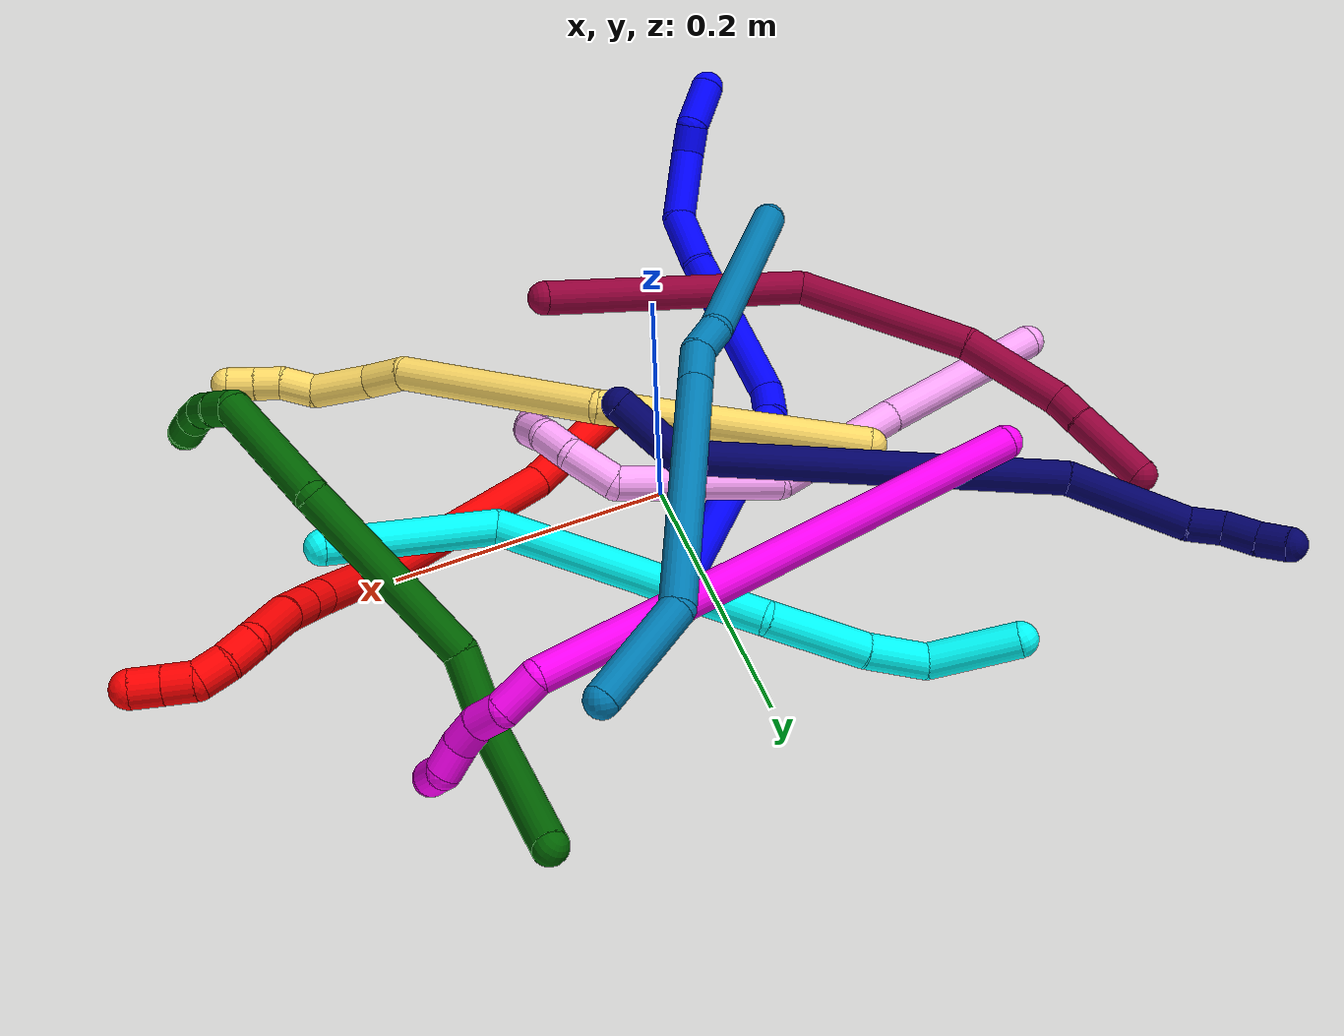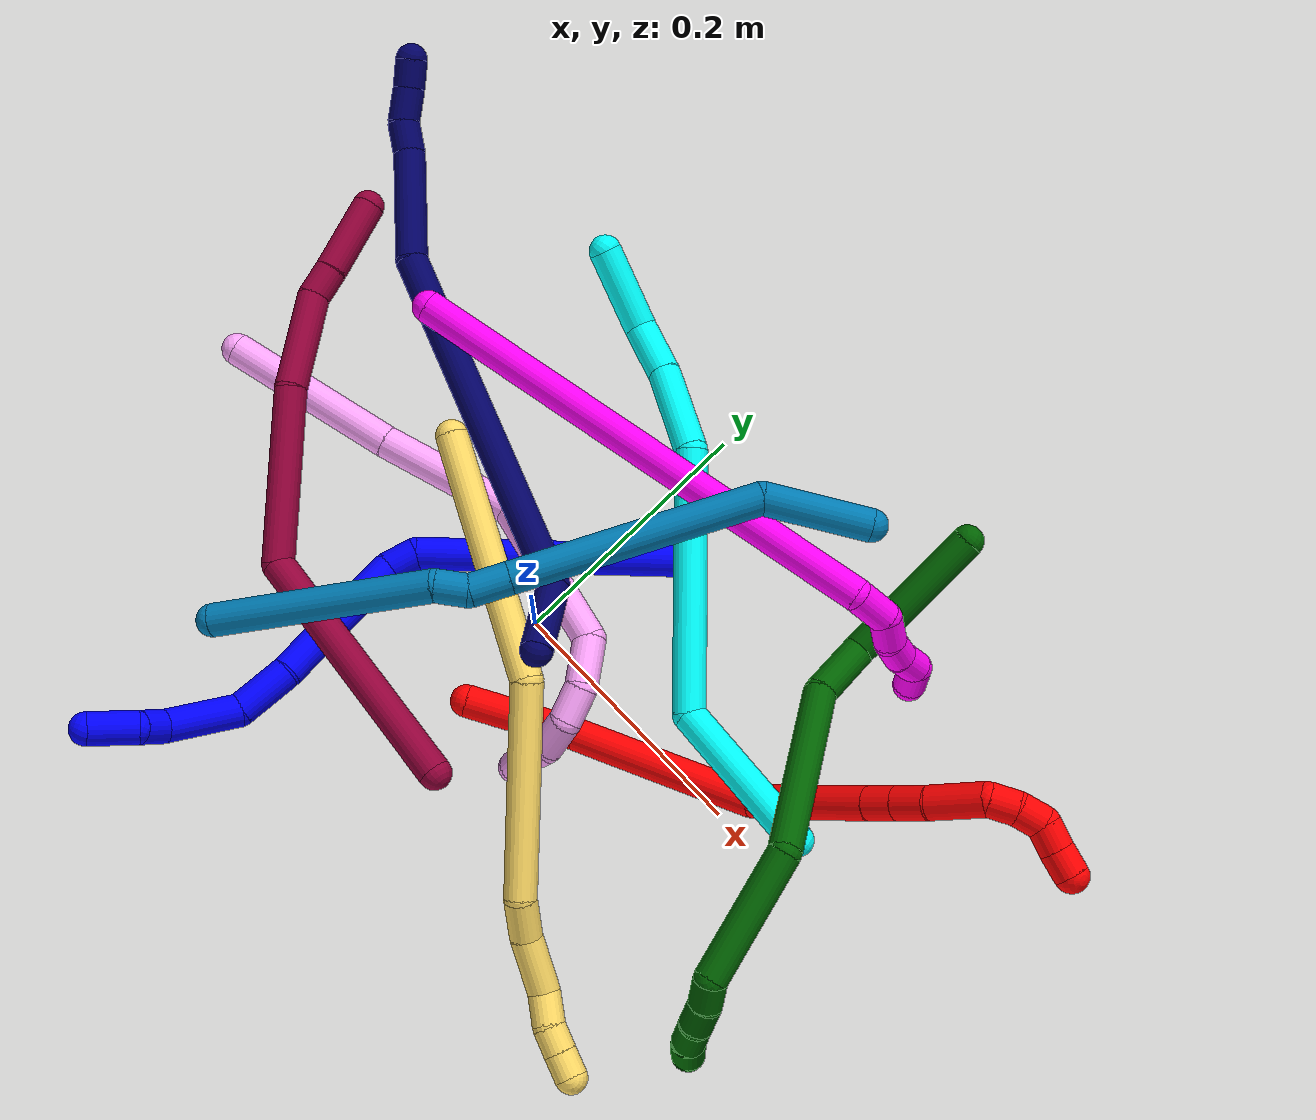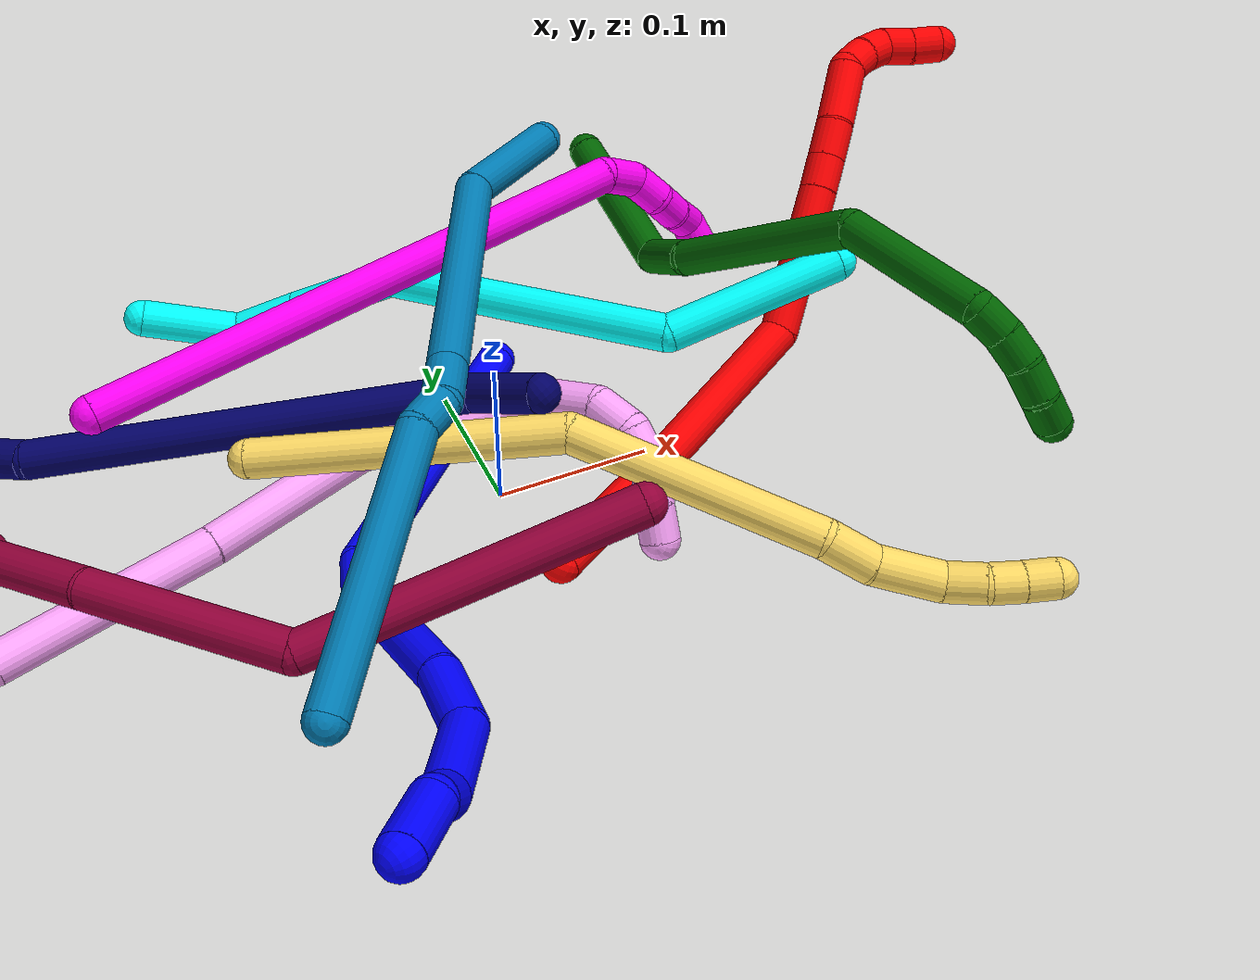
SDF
<sdf version="1.7">
 <world name="default">
  <plugin name="TubeGeneratorPlugin" filename="libtube_generator_plugin.so"/>
  <model name="photoneo_s_sensor">
   <static>1</static>
   <pose>0 0 2 1.57079 1.57079 3.14159</pose>
   <link name="link">
    <inertial><mass>0.1</mass></inertial>
    <sensor name="sensor" type="depth">
     <update_rate>30</update_rate>
     <camera>
      <horizontal_fov>1.22</horizontal_fov>
      <image><width>1920</width><height>1200</height><format>B8G8R8</format></image>
      <clip><near>0.1</near><far>4</far></clip>
      <depth_camera><output>points</output></depth_camera>
     </camera>
     <plugin name="camera_plugin" filename="libgazebo_ros_depth_camera.so">
      <baseline>0.2</baseline>
      <alwaysOn>1</alwaysOn>
      <updateRate>0.0</updateRate>
      <cameraName>camera_ir</cameraName>
      <imageTopicName>/camera/color/image_raw</imageTopicName>
      <cameraInfoTopicName>/camera/color/camera_info</cameraInfoTopicName>
      <depthImageTopicName>/camera/depth/image_raw</depthImageTopicName>
      <depthImageCameraInfoTopicName>/camera/depth/camera_info</depthImageCameraInfoTopicName>
      <pointCloudTopicName>/camera/depth/points</pointCloudTopicName>
      <frameName>fr_optical</frameName>
      <pointCloudCutoff>0.1</pointCloudCutoff>
      <pointCloudCutoffMax>2.0</pointCloudCutoffMax>
      <distortionK1>0</distortionK1>
      <distortionK2>0</distortionK2>
      <distortionK3>0</distortionK3>
      <distortionT1>0</distortionT1>
      <distortionT2>0</distortionT2>
      <CxPrime>0</CxPrime>
      <Cx>0</Cx>
      <Cy>0</Cy>
      <focalLength>0</focalLength>
      <hackBaseline>0</hackBaseline>
     </plugin>
    </sensor>
   </link>
  </model>
  <gravity>0 0 -9.8</gravity>
  <magnetic_field>6e-06 2.3e-05 -4.2e-05</magnetic_field>
  <atmosphere type="adiabatic"/>
  <physics name="default_physics" default="0" type="ode">
   <max_step_size>0.003</max_step_size>
   <real_time_factor>1</real_time_factor>
   <real_time_update_rate>1000</real_time_update_rate>
   <max_contacts>10000</max_contacts>
   <ode>
    <solver>
     <type>quick</type>
     <iters>100</iters>
     <sor>1.3</sor>
     <use_dynamic_moi_rescaling>0</use_dynamic_moi_rescaling>
    </solver>
    <constraints>
     <contact_max_correcting_vel>0</contact_max_correcting_vel>
     <contact_surface_layer>0.001</contact_surface_layer>
     <cfm>0</cfm>
     <erp>0.2</erp>
    </constraints>
   </ode>
  </physics>
  <scene><ambient>0.4 0.4 0.4 1</ambient><background>0.7 0.7 0.7 1</background><shadows>0</shadows></scene>
  <audio><device>default</device></audio>
  <spherical_coordinates>
   <surface_model>EARTH_WGS84</surface_model>
   <latitude_deg>0</latitude_deg>
   <longitude_deg>0</longitude_deg>
   <elevation>0</elevation>
   <heading_deg>0</heading_deg>
  </spherical_coordinates>
  <model name="bin">
   <static>1</static>
   <link name="bottom">
    <collision name="collision-bottom">
     <pose>0 0 -0.01 0 -0 0</pose>
     <geometry><box><size>0.8 0.6 0.02</size></box></geometry>
     <surface>
      <friction><ode><mu>100</mu><mu2>100</mu2></ode></friction>
      <contact><collide_bitmask>65535</collide_bitmask></contact>
     </surface>
    </collision>
   </link>
   <link name="west_wall">
    <collision name="collision-west_wall">
     <pose>-0.41 0 0.1 0 -0 0</pose>
     <geometry><box><size>0.02 0.6 0.2</size></box></geometry>
     <surface>
      <friction><ode><mu>100</mu><mu2>100</mu2></ode></friction>
      <contact><collide_bitmask>65535</collide_bitmask></contact>
     </surface>
    </collision>
   </link>
   <link name="east_wall">
    <collision name="collision-east_wall">
     <pose>0.41 0 0.1 0 -0 0</pose>
     <geometry><box><size>0.02 0.6 0.2</size></box></geometry>
     <surface>
      <friction><ode><mu>100</mu><mu2>100</mu2></ode></friction>
      <contact><collide_bitmask>65535</collide_bitmask></contact>
     </surface>
    </collision>
   </link>
   <link name="south_wall">
    <collision name="collision-south_wall">
     <pose>0 -0.31 0.1 0 -0 0</pose>
     <geometry><box><size>0.8 0.02 0.2</size></box></geometry>
     <surface>
      <friction><ode><mu>100</mu><mu2>100</mu2></ode></friction>
      <contact><collide_bitmask>65535</collide_bitmask></contact>
     </surface>
    </collision>
   </link>
   <link name="north_wall">
    <collision name="collision-north_wall">
     <pose>0 0.31 0.1 0 -0 0</pose>
     <geometry><box><size>0.8 0.02 0.2</size></box></geometry>
     <surface>
      <friction><ode><mu>100</mu><mu2>100</mu2></ode></friction>
      <contact><collide_bitmask>65535</collide_bitmask></contact>
     </surface>
    </collision>
   </link>
  </model>
  <model name="1">
   <static>0</static>
   <link name="1">
    <collision name="collision-cylinder-e_1_1_4">
     <pose>-0.025516 -0.025259 0.093465 0.26395 -0.257691 -0.034395</pose>
     <geometry><cylinder><radius>0.0125</radius><length>0.200248</length></cylinder></geometry>
     <surface>
      <friction><ode><mu>1.16</mu><mu2>1.16</mu2><slip1>0</slip1><slip2>0</slip2></ode></friction>
      <contact><ode><kp>1e+06</kp><kd>1</kd><max_vel>0</max_vel><min_depth>0.001</min_depth></ode></contact>
     </surface>
    </collision>
    <visual name="visual-cylinder-e_1_1_4">
     <pose>-0.025516 -0.025259 0.093465 0.26395 -0.257691 -0.034395</pose>
     <geometry><cylinder><radius>0.0125</radius><length>0.200248</length></cylinder></geometry>
     <material><ambient>0 0 1 1</ambient></material>
    </visual>
    <collision name="collision-cylinder-e_2_4_5">
     <pose>-0.056032 -0.058379 0.194829 0.782885 -0.421664 -0.176207</pose>
     <geometry><cylinder><radius>0.0125</radius><length>0.024427</length></cylinder></geometry>
     <surface>
      <friction><ode><mu>1.16</mu><mu2>1.16</mu2><slip1>0</slip1><slip2>0</slip2></ode></friction>
      <contact><ode><kp>1e+06</kp><kd>1</kd><max_vel>0</max_vel><min_depth>0.001</min_depth></ode></contact>
     </surface>
    </collision>
    <visual name="visual-cylinder-e_2_4_5">
     <pose>-0.056032 -0.058379 0.194829 0.782885 -0.421664 -0.176207</pose>
     <geometry><cylinder><radius>0.0125</radius><length>0.024427</length></cylinder></geometry>
     <material><ambient>0 0 1 1</ambient></material>
    </visual>
    <collision name="collision-cylinder-e_3_5_6">
     <pose>-0.067331 -0.11984 0.223192 1.2061 -0.109374 -0.075357</pose>
     <geometry><cylinder><radius>0.0125</radius><length>0.115439</length></cylinder></geometry>
     <surface>
      <friction><ode><mu>1.16</mu><mu2>1.16</mu2><slip1>0</slip1><slip2>0</slip2></ode></friction>
      <contact><ode><kp>1e+06</kp><kd>1</kd><max_vel>0</max_vel><min_depth>0.001</min_depth></ode></contact>
     </surface>
    </collision>
    <visual name="visual-cylinder-e_3_5_6">
     <pose>-0.067331 -0.11984 0.223192 1.2061 -0.109374 -0.075357</pose>
     <geometry><cylinder><radius>0.0125</radius><length>0.115439</length></cylinder></geometry>
     <material><ambient>0 0 1 1</ambient></material>
    </visual>
    <collision name="collision-cylinder-e_4_6_7">
     <pose>-0.079372 -0.191881 0.254097 1.05557 -0.26456 -0.15482</pose>
     <geometry><cylinder><radius>0.0125</radius><length>0.043909</length></cylinder></geometry>
     <surface>
      <friction><ode><mu>1.16</mu><mu2>1.16</mu2><slip1>0</slip1><slip2>0</slip2></ode></friction>
      <contact><ode><kp>1e+06</kp><kd>1</kd><max_vel>0</max_vel><min_depth>0.001</min_depth></ode></contact>
     </surface>
    </collision>
    <visual name="visual-cylinder-e_4_6_7">
     <pose>-0.079372 -0.191881 0.254097 1.05557 -0.26456 -0.15482</pose>
     <geometry><cylinder><radius>0.0125</radius><length>0.043909</length></cylinder></geometry>
     <material><ambient>0 0 1 1</ambient></material>
    </visual>
    <collision name="collision-cylinder-e_5_7_8">
     <pose>-0.086214 -0.226795 0.287335 0.625798 -0.039149 -0.012667</pose>
     <geometry><cylinder><radius>0.0125</radius><length>0.056297</length></cylinder></geometry>
     <surface>
      <friction><ode><mu>1.16</mu><mu2>1.16</mu2><slip1>0</slip1><slip2>0</slip2></ode></friction>
      <contact><ode><kp>1e+06</kp><kd>1</kd><max_vel>0</max_vel><min_depth>0.001</min_depth></ode></contact>
     </surface>
    </collision>
    <visual name="visual-cylinder-e_5_7_8">
     <pose>-0.086214 -0.226795 0.287335 0.625798 -0.039149 -0.012667</pose>
     <geometry><cylinder><radius>0.0125</radius><length>0.056297</length></cylinder></geometry>
     <material><ambient>0 0 1 1</ambient></material>
    </visual>
    <collision name="collision-cylinder-e_6_8_9">
     <pose>-0.082093 -0.249577 0.317727 0.692912 0.486672 0.178772</pose>
     <geometry><cylinder><radius>0.0125</radius><length>0.022338</length></cylinder></geometry>
     <surface>
      <friction><ode><mu>1.16</mu><mu2>1.16</mu2><slip1>0</slip1><slip2>0</slip2></ode></friction>
      <contact><ode><kp>1e+06</kp><kd>1</kd><max_vel>0</max_vel><min_depth>0.001</min_depth></ode></contact>
     </surface>
    </collision>
    <visual name="visual-cylinder-e_6_8_9">
     <pose>-0.082093 -0.249577 0.317727 0.692912 0.486672 0.178772</pose>
     <geometry><cylinder><radius>0.0125</radius><length>0.022338</length></cylinder></geometry>
     <material><ambient>0 0 1 1</ambient></material>
    </visual>
    <collision name="collision-cylinder-e_7_9_2">
     <pose>-0.077518 -0.263588 0.342317 0.425682 -0.034758 -0.007512</pose>
     <geometry><cylinder><radius>0.0125</radius><length>0.037343</length></cylinder></geometry>
     <surface>
      <friction><ode><mu>1.16</mu><mu2>1.16</mu2><slip1>0</slip1><slip2>0</slip2></ode></friction>
      <contact><ode><kp>1e+06</kp><kd>1</kd><max_vel>0</max_vel><min_depth>0.001</min_depth></ode></contact>
     </surface>
    </collision>
    <visual name="visual-cylinder-e_7_9_2">
     <pose>-0.077518 -0.263588 0.342317 0.425682 -0.034758 -0.007512</pose>
     <geometry><cylinder><radius>0.0125</radius><length>0.037343</length></cylinder></geometry>
     <material><ambient>0 0 1 1</ambient></material>
    </visual>
    <collision name="collision-sphere-2">
     <pose>-0.078167 -0.271294 0.359312 0 -0 0</pose>
     <geometry><sphere><radius>0.0125</radius></sphere></geometry>
     <surface>
      <friction><ode><mu>1.16</mu><mu2>1.16</mu2><slip1>0</slip1><slip2>0</slip2></ode></friction>
      <contact><ode><kp>1e+06</kp><kd>1</kd><max_vel>0</max_vel><min_depth>0.001</min_depth></ode></contact>
     </surface>
    </collision>
    <visual name="visual-sphere-2">
     <pose>-0.078167 -0.271294 0.359312 0 -0 0</pose>
     <geometry><sphere><radius>0.0125</radius></sphere></geometry>
     <material><ambient>0 0 1 1</ambient></material>
    </visual>
    <collision name="collision-sphere-9">
     <pose>-0.076869 -0.255883 0.325323 0 -0 0</pose>
     <geometry><sphere><radius>0.0125</radius></sphere></geometry>
     <surface>
      <friction><ode><mu>1.16</mu><mu2>1.16</mu2><slip1>0</slip1><slip2>0</slip2></ode></friction>
      <contact><ode><kp>1e+06</kp><kd>1</kd><max_vel>0</max_vel><min_depth>0.001</min_depth></ode></contact>
     </surface>
    </collision>
    <visual name="visual-sphere-9">
     <pose>-0.076869 -0.255883 0.325323 0 -0 0</pose>
     <geometry><sphere><radius>0.0125</radius></sphere></geometry>
     <material><ambient>0 0 1 1</ambient></material>
    </visual>
    <collision name="collision-sphere-4">
     <pose>-0.051033 -0.050519 0.18693 0 -0 0</pose>
     <geometry><sphere><radius>0.0125</radius></sphere></geometry>
     <surface>
      <friction><ode><mu>1.16</mu><mu2>1.16</mu2><slip1>0</slip1><slip2>0</slip2></ode></friction>
      <contact><ode><kp>1e+06</kp><kd>1</kd><max_vel>0</max_vel><min_depth>0.001</min_depth></ode></contact>
     </surface>
    </collision>
    <visual name="visual-sphere-4">
     <pose>-0.051033 -0.050519 0.18693 0 -0 0</pose>
     <geometry><sphere><radius>0.0125</radius></sphere></geometry>
     <material><ambient>0 0 1 1</ambient></material>
    </visual>
    <collision name="collision-sphere-1">
     <geometry><sphere><radius>0.0125</radius></sphere></geometry>
     <surface>
      <friction><ode><mu>1.16</mu><mu2>1.16</mu2><slip1>0</slip1><slip2>0</slip2></ode></friction>
      <contact><ode><kp>1e+06</kp><kd>1</kd><max_vel>0</max_vel><min_depth>0.001</min_depth></ode></contact>
     </surface>
    </collision>
    <visual name="visual-sphere-1">
     <geometry><sphere><radius>0.0125</radius></sphere></geometry>
     <material><ambient>0 0 1 1</ambient></material>
    </visual>
    <collision name="collision-sphere-8">
     <pose>-0.087316 -0.243271 0.310132 0 -0 0</pose>
     <geometry><sphere><radius>0.0125</radius></sphere></geometry>
     <surface>
      <friction><ode><mu>1.16</mu><mu2>1.16</mu2><slip1>0</slip1><slip2>0</slip2></ode></friction>
      <contact><ode><kp>1e+06</kp><kd>1</kd><max_vel>0</max_vel><min_depth>0.001</min_depth></ode></contact>
     </surface>
    </collision>
    <visual name="visual-sphere-8">
     <pose>-0.087316 -0.243271 0.310132 0 -0 0</pose>
     <geometry><sphere><radius>0.0125</radius></sphere></geometry>
     <material><ambient>0 0 1 1</ambient></material>
    </visual>
    <collision name="collision-sphere-5">
     <pose>-0.06103 -0.066239 0.202729 0 -0 0</pose>
     <geometry><sphere><radius>0.0125</radius></sphere></geometry>
     <surface>
      <friction><ode><mu>1.16</mu><mu2>1.16</mu2><slip1>0</slip1><slip2>0</slip2></ode></friction>
      <contact><ode><kp>1e+06</kp><kd>1</kd><max_vel>0</max_vel><min_depth>0.001</min_depth></ode></contact>
     </surface>
    </collision>
    <visual name="visual-sphere-5">
     <pose>-0.06103 -0.066239 0.202729 0 -0 0</pose>
     <geometry><sphere><radius>0.0125</radius></sphere></geometry>
     <material><ambient>0 0 1 1</ambient></material>
    </visual>
    <collision name="collision-sphere-6">
     <pose>-0.073631 -0.173441 0.243655 0 -0 0</pose>
     <geometry><sphere><radius>0.0125</radius></sphere></geometry>
     <surface>
      <friction><ode><mu>1.16</mu><mu2>1.16</mu2><slip1>0</slip1><slip2>0</slip2></ode></friction>
      <contact><ode><kp>1e+06</kp><kd>1</kd><max_vel>0</max_vel><min_depth>0.001</min_depth></ode></contact>
     </surface>
    </collision>
    <visual name="visual-sphere-6">
     <pose>-0.073631 -0.173441 0.243655 0 -0 0</pose>
     <geometry><sphere><radius>0.0125</radius></sphere></geometry>
     <material><ambient>0 0 1 1</ambient></material>
    </visual>
    <collision name="collision-sphere-7">
     <pose>-0.085113 -0.21032 0.264538 0 -0 0</pose>
     <geometry><sphere><radius>0.0125</radius></sphere></geometry>
     <surface>
      <friction><ode><mu>1.16</mu><mu2>1.16</mu2><slip1>0</slip1><slip2>0</slip2></ode></friction>
      <contact><ode><kp>1e+06</kp><kd>1</kd><max_vel>0</max_vel><min_depth>0.001</min_depth></ode></contact>
     </surface>
    </collision>
    <visual name="visual-sphere-7">
     <pose>-0.085113 -0.21032 0.264538 0 -0 0</pose>
     <geometry><sphere><radius>0.0125</radius></sphere></geometry>
     <material><ambient>0 0 1 1</ambient></material>
    </visual>
    <inertial>
     <pose>-0.054636 -0.113859 0.192908 0 -0 0</pose>
     <mass>0.5</mass>
     <inertia>
      <ixx>0.00078</ixx>
      <ixy>0</ixy>
      <ixz>0</ixz>
      <iyy>0.000674</iyy>
      <iyz>0</iyz>
      <izz>0.000534</izz>
     </inertia>
    </inertial>
   </link>
   <pose>0.042143 0.111805 0.012053 -1.28609 -1.10614 1.75072</pose>
  </model>
  <model name="2">
   <static>0</static>
   <link name="2">
    <collision name="collision-cylinder-e_1_1_4">
     <pose>0.025647 0.022432 0.025403 -0.723371 0.647817 -0.252682</pose>
     <geometry><cylinder><radius>0.0125</radius><length>0.085001</length></cylinder></geometry>
     <surface>
      <friction><ode><mu>1.16</mu><mu2>1.16</mu2><slip1>0</slip1><slip2>0</slip2></ode></friction>
      <contact><ode><kp>1e+06</kp><kd>1</kd><max_vel>0</max_vel><min_depth>0.001</min_depth></ode></contact>
     </surface>
    </collision>
    <visual name="visual-cylinder-e_1_1_4">
     <pose>0.025647 0.022432 0.025403 -0.723371 0.647817 -0.252682</pose>
     <geometry><cylinder><radius>0.0125</radius><length>0.085001</length></cylinder></geometry>
     <material><ambient>1 0 0 1</ambient></material>
    </visual>
    <collision name="collision-cylinder-e_2_4_5">
     <pose>0.088349 0.072956 0.105535 -0.474216 0.542153 -0.134118</pose>
     <geometry><cylinder><radius>0.0125</radius><length>0.143631</length></cylinder></geometry>
     <surface>
      <friction><ode><mu>1.16</mu><mu2>1.16</mu2><slip1>0</slip1><slip2>0</slip2></ode></friction>
      <contact><ode><kp>1e+06</kp><kd>1</kd><max_vel>0</max_vel><min_depth>0.001</min_depth></ode></contact>
     </surface>
    </collision>
    <visual name="visual-cylinder-e_2_4_5">
     <pose>0.088349 0.072956 0.105535 -0.474216 0.542153 -0.134118</pose>
     <geometry><cylinder><radius>0.0125</radius><length>0.143631</length></cylinder></geometry>
     <material><ambient>1 0 0 1</ambient></material>
    </visual>
    <collision name="collision-cylinder-e_3_5_6">
     <pose>0.125526 0.119895 0.206271 -0.388817 0.002455 -0.000483</pose>
     <geometry><cylinder><radius>0.0125</radius><length>0.099436</length></cylinder></geometry>
     <surface>
      <friction><ode><mu>1.16</mu><mu2>1.16</mu2><slip1>0</slip1><slip2>0</slip2></ode></friction>
      <contact><ode><kp>1e+06</kp><kd>1</kd><max_vel>0</max_vel><min_depth>0.001</min_depth></ode></contact>
     </surface>
    </collision>
    <visual name="visual-cylinder-e_3_5_6">
     <pose>0.125526 0.119895 0.206271 -0.388817 0.002455 -0.000483</pose>
     <geometry><cylinder><radius>0.0125</radius><length>0.099436</length></cylinder></geometry>
     <material><ambient>1 0 0 1</ambient></material>
    </visual>
    <collision name="collision-cylinder-e_4_6_7">
     <pose>0.125604 0.143378 0.262735 -0.41728 -0.003862 0.000818</pose>
     <geometry><cylinder><radius>0.0125</radius><length>0.022878</length></cylinder></geometry>
     <surface>
      <friction><ode><mu>1.16</mu><mu2>1.16</mu2><slip1>0</slip1><slip2>0</slip2></ode></friction>
      <contact><ode><kp>1e+06</kp><kd>1</kd><max_vel>0</max_vel><min_depth>0.001</min_depth></ode></contact>
     </surface>
    </collision>
    <visual name="visual-cylinder-e_4_6_7">
     <pose>0.125604 0.143378 0.262735 -0.41728 -0.003862 0.000818</pose>
     <geometry><cylinder><radius>0.0125</radius><length>0.022878</length></cylinder></geometry>
     <material><ambient>1 0 0 1</ambient></material>
    </visual>
    <collision name="collision-cylinder-e_5_7_8">
     <pose>0.125503 0.153123 0.284691 -0.418093 -0.004511 0.000957</pose>
     <geometry><cylinder><radius>0.0125</radius><length>0.025166</length></cylinder></geometry>
     <surface>
      <friction><ode><mu>1.16</mu><mu2>1.16</mu2><slip1>0</slip1><slip2>0</slip2></ode></friction>
      <contact><ode><kp>1e+06</kp><kd>1</kd><max_vel>0</max_vel><min_depth>0.001</min_depth></ode></contact>
     </surface>
    </collision>
    <visual name="visual-cylinder-e_5_7_8">
     <pose>0.125503 0.153123 0.284691 -0.418093 -0.004511 0.000957</pose>
     <geometry><cylinder><radius>0.0125</radius><length>0.025166</length></cylinder></geometry>
     <material><ambient>1 0 0 1</ambient></material>
    </visual>
    <collision name="collision-cylinder-e_6_8_9">
     <pose>0.126559 0.169566 0.314464 -0.555161 0.051672 -0.014726</pose>
     <geometry><cylinder><radius>0.0125</radius><length>0.043066</length></cylinder></geometry>
     <surface>
      <friction><ode><mu>1.16</mu><mu2>1.16</mu2><slip1>0</slip1><slip2>0</slip2></ode></friction>
      <contact><ode><kp>1e+06</kp><kd>1</kd><max_vel>0</max_vel><min_depth>0.001</min_depth></ode></contact>
     </surface>
    </collision>
    <visual name="visual-cylinder-e_6_8_9">
     <pose>0.126559 0.169566 0.314464 -0.555161 0.051672 -0.014726</pose>
     <geometry><cylinder><radius>0.0125</radius><length>0.043066</length></cylinder></geometry>
     <material><ambient>1 0 0 1</ambient></material>
    </visual>
    <collision name="collision-cylinder-e_7_9_10">
     <pose>0.133729 0.186097 0.339348 -0.66632 0.624388 -0.222458</pose>
     <geometry><cylinder><radius>0.0125</radius><length>0.020726</length></cylinder></geometry>
     <surface>
      <friction><ode><mu>1.16</mu><mu2>1.16</mu2><slip1>0</slip1><slip2>0</slip2></ode></friction>
      <contact><ode><kp>1e+06</kp><kd>1</kd><max_vel>0</max_vel><min_depth>0.001</min_depth></ode></contact>
     </surface>
    </collision>
    <visual name="visual-cylinder-e_7_9_10">
     <pose>0.133729 0.186097 0.339348 -0.66632 0.624388 -0.222458</pose>
     <geometry><cylinder><radius>0.0125</radius><length>0.020726</length></cylinder></geometry>
     <material><ambient>1 0 0 1</ambient></material>
    </visual>
    <collision name="collision-cylinder-e_8_10_11">
     <pose>0.147235 0.194829 0.35163 -0.557338 0.839411 -0.253965</pose>
     <geometry><cylinder><radius>0.0125</radius><length>0.020014</length></cylinder></geometry>
     <surface>
      <friction><ode><mu>1.16</mu><mu2>1.16</mu2><slip1>0</slip1><slip2>0</slip2></ode></friction>
      <contact><ode><kp>1e+06</kp><kd>1</kd><max_vel>0</max_vel><min_depth>0.001</min_depth></ode></contact>
     </surface>
    </collision>
    <visual name="visual-cylinder-e_8_10_11">
     <pose>0.147235 0.194829 0.35163 -0.557338 0.839411 -0.253965</pose>
     <geometry><cylinder><radius>0.0125</radius><length>0.020014</length></cylinder></geometry>
     <material><ambient>1 0 0 1</ambient></material>
    </visual>
    <collision name="collision-cylinder-e_9_11_12">
     <pose>0.163576 0.196403 0.361477 0.439104 1.09231 0.269627</pose>
     <geometry><cylinder><radius>0.0125</radius><length>0.020038</length></cylinder></geometry>
     <surface>
      <friction><ode><mu>1.16</mu><mu2>1.16</mu2><slip1>0</slip1><slip2>0</slip2></ode></friction>
      <contact><ode><kp>1e+06</kp><kd>1</kd><max_vel>0</max_vel><min_depth>0.001</min_depth></ode></contact>
     </surface>
    </collision>
    <visual name="visual-cylinder-e_9_11_12">
     <pose>0.163576 0.196403 0.361477 0.439104 1.09231 0.269627</pose>
     <geometry><cylinder><radius>0.0125</radius><length>0.020038</length></cylinder></geometry>
     <material><ambient>1 0 0 1</ambient></material>
    </visual>
    <collision name="collision-cylinder-e_10_12_2">
     <pose>0.180929 0.192706 0.37074 0.328909 1.00475 0.181843</pose>
     <geometry><cylinder><radius>0.0125</radius><length>0.020046</length></cylinder></geometry>
     <surface>
      <friction><ode><mu>1.16</mu><mu2>1.16</mu2><slip1>0</slip1><slip2>0</slip2></ode></friction>
      <contact><ode><kp>1e+06</kp><kd>1</kd><max_vel>0</max_vel><min_depth>0.001</min_depth></ode></contact>
     </surface>
    </collision>
    <visual name="visual-cylinder-e_10_12_2">
     <pose>0.180929 0.192706 0.37074 0.328909 1.00475 0.181843</pose>
     <geometry><cylinder><radius>0.0125</radius><length>0.020046</length></cylinder></geometry>
     <material><ambient>1 0 0 1</ambient></material>
    </visual>
    <collision name="collision-sphere-2">
     <pose>0.189389 0.19097 0.375827 0 -0 0</pose>
     <geometry><sphere><radius>0.0125</radius></sphere></geometry>
     <surface>
      <friction><ode><mu>1.16</mu><mu2>1.16</mu2><slip1>0</slip1><slip2>0</slip2></ode></friction>
      <contact><ode><kp>1e+06</kp><kd>1</kd><max_vel>0</max_vel><min_depth>0.001</min_depth></ode></contact>
     </surface>
    </collision>
    <visual name="visual-sphere-2">
     <pose>0.189389 0.19097 0.375827 0 -0 0</pose>
     <geometry><sphere><radius>0.0125</radius></sphere></geometry>
     <material><ambient>1 0 0 1</ambient></material>
    </visual>
    <collision name="collision-sphere-12">
     <pose>0.17247 0.194442 0.365653 0 -0 0</pose>
     <geometry><sphere><radius>0.0125</radius></sphere></geometry>
     <surface>
      <friction><ode><mu>1.16</mu><mu2>1.16</mu2><slip1>0</slip1><slip2>0</slip2></ode></friction>
      <contact><ode><kp>1e+06</kp><kd>1</kd><max_vel>0</max_vel><min_depth>0.001</min_depth></ode></contact>
     </surface>
    </collision>
    <visual name="visual-sphere-12">
     <pose>0.17247 0.194442 0.365653 0 -0 0</pose>
     <geometry><sphere><radius>0.0125</radius></sphere></geometry>
     <material><ambient>1 0 0 1</ambient></material>
    </visual>
    <collision name="collision-sphere-11">
     <pose>0.154683 0.198365 0.357302 0 -0 0</pose>
     <geometry><sphere><radius>0.0125</radius></sphere></geometry>
     <surface>
      <friction><ode><mu>1.16</mu><mu2>1.16</mu2><slip1>0</slip1><slip2>0</slip2></ode></friction>
      <contact><ode><kp>1e+06</kp><kd>1</kd><max_vel>0</max_vel><min_depth>0.001</min_depth></ode></contact>
     </surface>
    </collision>
    <visual name="visual-sphere-11">
     <pose>0.154683 0.198365 0.357302 0 -0 0</pose>
     <geometry><sphere><radius>0.0125</radius></sphere></geometry>
     <material><ambient>1 0 0 1</ambient></material>
    </visual>
    <collision name="collision-sphere-10">
     <pose>0.139787 0.191294 0.345958 0 -0 0</pose>
     <geometry><sphere><radius>0.0125</radius></sphere></geometry>
     <surface>
      <friction><ode><mu>1.16</mu><mu2>1.16</mu2><slip1>0</slip1><slip2>0</slip2></ode></friction>
      <contact><ode><kp>1e+06</kp><kd>1</kd><max_vel>0</max_vel><min_depth>0.001</min_depth></ode></contact>
     </surface>
    </collision>
    <visual name="visual-sphere-10">
     <pose>0.139787 0.191294 0.345958 0 -0 0</pose>
     <geometry><sphere><radius>0.0125</radius></sphere></geometry>
     <material><ambient>1 0 0 1</ambient></material>
    </visual>
    <collision name="collision-sphere-9">
     <pose>0.127671 0.180901 0.332739 0 -0 0</pose>
     <geometry><sphere><radius>0.0125</radius></sphere></geometry>
     <surface>
      <friction><ode><mu>1.16</mu><mu2>1.16</mu2><slip1>0</slip1><slip2>0</slip2></ode></friction>
      <contact><ode><kp>1e+06</kp><kd>1</kd><max_vel>0</max_vel><min_depth>0.001</min_depth></ode></contact>
     </surface>
    </collision>
    <visual name="visual-sphere-9">
     <pose>0.127671 0.180901 0.332739 0 -0 0</pose>
     <geometry><sphere><radius>0.0125</radius></sphere></geometry>
     <material><ambient>1 0 0 1</ambient></material>
    </visual>
    <collision name="collision-sphere-4">
     <pose>0.051293 0.044865 0.050806 0 -0 0</pose>
     <geometry><sphere><radius>0.0125</radius></sphere></geometry>
     <surface>
      <friction><ode><mu>1.16</mu><mu2>1.16</mu2><slip1>0</slip1><slip2>0</slip2></ode></friction>
      <contact><ode><kp>1e+06</kp><kd>1</kd><max_vel>0</max_vel><min_depth>0.001</min_depth></ode></contact>
     </surface>
    </collision>
    <visual name="visual-sphere-4">
     <pose>0.051293 0.044865 0.050806 0 -0 0</pose>
     <geometry><sphere><radius>0.0125</radius></sphere></geometry>
     <material><ambient>1 0 0 1</ambient></material>
    </visual>
    <collision name="collision-sphere-1">
     <geometry><sphere><radius>0.0125</radius></sphere></geometry>
     <surface>
      <friction><ode><mu>1.16</mu><mu2>1.16</mu2><slip1>0</slip1><slip2>0</slip2></ode></friction>
      <contact><ode><kp>1e+06</kp><kd>1</kd><max_vel>0</max_vel><min_depth>0.001</min_depth></ode></contact>
     </surface>
    </collision>
    <visual name="visual-sphere-1">
     <geometry><sphere><radius>0.0125</radius></sphere></geometry>
     <material><ambient>1 0 0 1</ambient></material>
    </visual>
    <collision name="collision-sphere-8">
     <pose>0.125447 0.158232 0.29619 0 -0 0</pose>
     <geometry><sphere><radius>0.0125</radius></sphere></geometry>
     <surface>
      <friction><ode><mu>1.16</mu><mu2>1.16</mu2><slip1>0</slip1><slip2>0</slip2></ode></friction>
      <contact><ode><kp>1e+06</kp><kd>1</kd><max_vel>0</max_vel><min_depth>0.001</min_depth></ode></contact>
     </surface>
    </collision>
    <visual name="visual-sphere-8">
     <pose>0.125447 0.158232 0.29619 0 -0 0</pose>
     <geometry><sphere><radius>0.0125</radius></sphere></geometry>
     <material><ambient>1 0 0 1</ambient></material>
    </visual>
    <collision name="collision-sphere-5">
     <pose>0.125404 0.101047 0.160264 0 -0 0</pose>
     <geometry><sphere><radius>0.0125</radius></sphere></geometry>
     <surface>
      <friction><ode><mu>1.16</mu><mu2>1.16</mu2><slip1>0</slip1><slip2>0</slip2></ode></friction>
      <contact><ode><kp>1e+06</kp><kd>1</kd><max_vel>0</max_vel><min_depth>0.001</min_depth></ode></contact>
     </surface>
    </collision>
    <visual name="visual-sphere-5">
     <pose>0.125404 0.101047 0.160264 0 -0 0</pose>
     <geometry><sphere><radius>0.0125</radius></sphere></geometry>
     <material><ambient>1 0 0 1</ambient></material>
    </visual>
    <collision name="collision-sphere-6">
     <pose>0.125648 0.138743 0.252278 0 -0 0</pose>
     <geometry><sphere><radius>0.0125</radius></sphere></geometry>
     <surface>
      <friction><ode><mu>1.16</mu><mu2>1.16</mu2><slip1>0</slip1><slip2>0</slip2></ode></friction>
      <contact><ode><kp>1e+06</kp><kd>1</kd><max_vel>0</max_vel><min_depth>0.001</min_depth></ode></contact>
     </surface>
    </collision>
    <visual name="visual-sphere-6">
     <pose>0.125648 0.138743 0.252278 0 -0 0</pose>
     <geometry><sphere><radius>0.0125</radius></sphere></geometry>
     <material><ambient>1 0 0 1</ambient></material>
    </visual>
    <collision name="collision-sphere-7">
     <pose>0.12556 0.148014 0.273192 0 -0 0</pose>
     <geometry><sphere><radius>0.0125</radius></sphere></geometry>
     <surface>
      <friction><ode><mu>1.16</mu><mu2>1.16</mu2><slip1>0</slip1><slip2>0</slip2></ode></friction>
      <contact><ode><kp>1e+06</kp><kd>1</kd><max_vel>0</max_vel><min_depth>0.001</min_depth></ode></contact>
     </surface>
    </collision>
    <visual name="visual-sphere-7">
     <pose>0.12556 0.148014 0.273192 0 -0 0</pose>
     <geometry><sphere><radius>0.0125</radius></sphere></geometry>
     <material><ambient>1 0 0 1</ambient></material>
    </visual>
    <inertial>
     <pose>0.102913 0.108596 0.186583 0 -0 0</pose>
     <mass>0.5</mass>
     <inertia>
      <ixx>0.000333</ixx>
      <ixy>0</ixy>
      <ixz>0</ixz>
      <iyy>0.000346</iyy>
      <iyz>0</iyz>
      <izz>-0.000306</izz>
     </inertia>
    </inertial>
   </link>
   <pose>0.007417 -0.078514 0.011493 -0.335859 0.552665 -0.255516</pose>
  </model>
  <model name="3">
   <static>0</static>
   <link name="3">
    <collision name="collision-cylinder-e_1_1_4">
     <pose>-0.019521 0.005413 0.056515 -0.095485 -0.331172 0.015969</pose>
     <geometry><cylinder><radius>0.0125</radius><length>0.120072</length></cylinder></geometry>
     <surface>
      <friction><ode><mu>1.16</mu><mu2>1.16</mu2><slip1>0</slip1><slip2>0</slip2></ode></friction>
      <contact><ode><kp>1e+06</kp><kd>1</kd><max_vel>0</max_vel><min_depth>0.001</min_depth></ode></contact>
     </surface>
    </collision>
    <visual name="visual-cylinder-e_1_1_4">
     <pose>-0.019521 0.005413 0.056515 -0.095485 -0.331172 0.015969</pose>
     <geometry><cylinder><radius>0.0125</radius><length>0.120072</length></cylinder></geometry>
     <material><ambient>0.003922 1 0.996078 1</ambient></material>
    </visual>
    <collision name="collision-cylinder-e_2_4_5">
     <pose>-0.080715 0.078914 0.170347 -0.871089 -0.437916 0.206368</pose>
     <geometry><cylinder><radius>0.0125</radius><length>0.19655</length></cylinder></geometry>
     <surface>
      <friction><ode><mu>1.16</mu><mu2>1.16</mu2><slip1>0</slip1><slip2>0</slip2></ode></friction>
      <contact><ode><kp>1e+06</kp><kd>1</kd><max_vel>0</max_vel><min_depth>0.001</min_depth></ode></contact>
     </surface>
    </collision>
    <visual name="visual-cylinder-e_2_4_5">
     <pose>-0.080715 0.078914 0.170347 -0.871089 -0.437916 0.206368</pose>
     <geometry><cylinder><radius>0.0125</radius><length>0.19655</length></cylinder></geometry>
     <material><ambient>0.003922 1 0.996078 1</ambient></material>
    </visual>
    <collision name="collision-cylinder-e_3_5_6">
     <pose>-0.145326 0.157636 0.253656 -0.388298 -0.684856 0.139954</pose>
     <geometry><cylinder><radius>0.0125</radius><length>0.072519</length></cylinder></geometry>
     <surface>
      <friction><ode><mu>1.16</mu><mu2>1.16</mu2><slip1>0</slip1><slip2>0</slip2></ode></friction>
      <contact><ode><kp>1e+06</kp><kd>1</kd><max_vel>0</max_vel><min_depth>0.001</min_depth></ode></contact>
     </surface>
    </collision>
    <visual name="visual-cylinder-e_3_5_6">
     <pose>-0.145326 0.157636 0.253656 -0.388298 -0.684856 0.139954</pose>
     <geometry><cylinder><radius>0.0125</radius><length>0.072519</length></cylinder></geometry>
     <material><ambient>0.003922 1 0.996078 1</ambient></material>
    </visual>
    <collision name="collision-cylinder-e_4_6_7">
     <pose>-0.180811 0.173369 0.297982 -0.271329 -0.582999 0.081869</pose>
     <geometry><cylinder><radius>0.0125</radius><length>0.045588</length></cylinder></geometry>
     <surface>
      <friction><ode><mu>1.16</mu><mu2>1.16</mu2><slip1>0</slip1><slip2>0</slip2></ode></friction>
      <contact><ode><kp>1e+06</kp><kd>1</kd><max_vel>0</max_vel><min_depth>0.001</min_depth></ode></contact>
     </surface>
    </collision>
    <visual name="visual-cylinder-e_4_6_7">
     <pose>-0.180811 0.173369 0.297982 -0.271329 -0.582999 0.081869</pose>
     <geometry><cylinder><radius>0.0125</radius><length>0.045588</length></cylinder></geometry>
     <material><ambient>0.003922 1 0.996078 1</ambient></material>
    </visual>
    <collision name="collision-cylinder-e_5_7_2">
     <pose>-0.193212 0.194954 0.34448 -0.529539 0.004545 -0.001232</pose>
     <geometry><cylinder><radius>0.0125</radius><length>0.06527</length></cylinder></geometry>
     <surface>
      <friction><ode><mu>1.16</mu><mu2>1.16</mu2><slip1>0</slip1><slip2>0</slip2></ode></friction>
      <contact><ode><kp>1e+06</kp><kd>1</kd><max_vel>0</max_vel><min_depth>0.001</min_depth></ode></contact>
     </surface>
    </collision>
    <visual name="visual-cylinder-e_5_7_2">
     <pose>-0.193212 0.194954 0.34448 -0.529539 0.004545 -0.001232</pose>
     <geometry><cylinder><radius>0.0125</radius><length>0.06527</length></cylinder></geometry>
     <material><ambient>0.003922 1 0.996078 1</ambient></material>
    </visual>
    <collision name="collision-sphere-2">
     <pose>-0.193063 0.211439 0.372645 0 -0 0</pose>
     <geometry><sphere><radius>0.0125</radius></sphere></geometry>
     <surface>
      <friction><ode><mu>1.16</mu><mu2>1.16</mu2><slip1>0</slip1><slip2>0</slip2></ode></friction>
      <contact><ode><kp>1e+06</kp><kd>1</kd><max_vel>0</max_vel><min_depth>0.001</min_depth></ode></contact>
     </surface>
    </collision>
    <visual name="visual-sphere-2">
     <pose>-0.193063 0.211439 0.372645 0 -0 0</pose>
     <geometry><sphere><radius>0.0125</radius></sphere></geometry>
     <material><ambient>0.003922 1 0.996078 1</ambient></material>
    </visual>
    <collision name="collision-sphere-7">
     <pose>-0.19336 0.178469 0.316315 0 -0 0</pose>
     <geometry><sphere><radius>0.0125</radius></sphere></geometry>
     <surface>
      <friction><ode><mu>1.16</mu><mu2>1.16</mu2><slip1>0</slip1><slip2>0</slip2></ode></friction>
      <contact><ode><kp>1e+06</kp><kd>1</kd><max_vel>0</max_vel><min_depth>0.001</min_depth></ode></contact>
     </surface>
    </collision>
    <visual name="visual-sphere-7">
     <pose>-0.19336 0.178469 0.316315 0 -0 0</pose>
     <geometry><sphere><radius>0.0125</radius></sphere></geometry>
     <material><ambient>0.003922 1 0.996078 1</ambient></material>
    </visual>
    <collision name="collision-sphere-6">
     <pose>-0.168262 0.168269 0.279649 0 -0 0</pose>
     <geometry><sphere><radius>0.0125</radius></sphere></geometry>
     <surface>
      <friction><ode><mu>1.16</mu><mu2>1.16</mu2><slip1>0</slip1><slip2>0</slip2></ode></friction>
      <contact><ode><kp>1e+06</kp><kd>1</kd><max_vel>0</max_vel><min_depth>0.001</min_depth></ode></contact>
     </surface>
    </collision>
    <visual name="visual-sphere-6">
     <pose>-0.168262 0.168269 0.279649 0 -0 0</pose>
     <geometry><sphere><radius>0.0125</radius></sphere></geometry>
     <material><ambient>0.003922 1 0.996078 1</ambient></material>
    </visual>
    <collision name="collision-sphere-5">
     <pose>-0.122389 0.147003 0.227663 0 -0 0</pose>
     <geometry><sphere><radius>0.0125</radius></sphere></geometry>
     <surface>
      <friction><ode><mu>1.16</mu><mu2>1.16</mu2><slip1>0</slip1><slip2>0</slip2></ode></friction>
      <contact><ode><kp>1e+06</kp><kd>1</kd><max_vel>0</max_vel><min_depth>0.001</min_depth></ode></contact>
     </surface>
    </collision>
    <visual name="visual-sphere-5">
     <pose>-0.122389 0.147003 0.227663 0 -0 0</pose>
     <geometry><sphere><radius>0.0125</radius></sphere></geometry>
     <material><ambient>0.003922 1 0.996078 1</ambient></material>
    </visual>
    <collision name="collision-sphere-1">
     <geometry><sphere><radius>0.0125</radius></sphere></geometry>
     <surface>
      <friction><ode><mu>1.16</mu><mu2>1.16</mu2><slip1>0</slip1><slip2>0</slip2></ode></friction>
      <contact><ode><kp>1e+06</kp><kd>1</kd><max_vel>0</max_vel><min_depth>0.001</min_depth></ode></contact>
     </surface>
    </collision>
    <visual name="visual-sphere-1">
     <geometry><sphere><radius>0.0125</radius></sphere></geometry>
     <material><ambient>0.003922 1 0.996078 1</ambient></material>
    </visual>
    <collision name="collision-sphere-4">
     <pose>-0.039042 0.010826 0.113031 0 -0 0</pose>
     <geometry><sphere><radius>0.0125</radius></sphere></geometry>
     <surface>
      <friction><ode><mu>1.16</mu><mu2>1.16</mu2><slip1>0</slip1><slip2>0</slip2></ode></friction>
      <contact><ode><kp>1e+06</kp><kd>1</kd><max_vel>0</max_vel><min_depth>0.001</min_depth></ode></contact>
     </surface>
    </collision>
    <visual name="visual-sphere-4">
     <pose>-0.039042 0.010826 0.113031 0 -0 0</pose>
     <geometry><sphere><radius>0.0125</radius></sphere></geometry>
     <material><ambient>0.003922 1 0.996078 1</ambient></material>
    </visual>
    <inertial>
     <pose>-0.099203 0.096441 0.189463 0 -0 0</pose>
     <mass>0.5</mass>
     <inertia>
      <ixx>0.000879</ixx>
      <ixy>0</ixy>
      <ixz>0</ixz>
      <iyy>0.000801</iyy>
      <iyz>0</iyz>
      <izz>-0.000106</izz>
     </inertia>
    </inertial>
   </link>
   <pose>0.247465 0.022883 0.090828 1.52263 -1.07782 -1.35956</pose>
  </model>
  <model name="4">
   <static>0</static>
   <link name="4">
    <collision name="collision-cylinder-e_1_1_4">
     <pose>0.046849 0.014359 -0.047673 -2.84904 0.754995 -2.43009</pose>
     <geometry><cylinder><radius>0.0125</radius><length>0.13673</length></cylinder></geometry>
     <surface>
      <friction><ode><mu>1.16</mu><mu2>1.16</mu2><slip1>0</slip1><slip2>0</slip2></ode></friction>
      <contact><ode><kp>1e+06</kp><kd>1</kd><max_vel>0</max_vel><min_depth>0.001</min_depth></ode></contact>
     </surface>
    </collision>
    <visual name="visual-cylinder-e_1_1_4">
     <pose>0.046849 0.014359 -0.047673 -2.84904 0.754995 -2.43009</pose>
     <geometry><cylinder><radius>0.0125</radius><length>0.13673</length></cylinder></geometry>
     <material><ambient>1 0.65098 0.996078 1</ambient></material>
    </visual>
    <collision name="collision-cylinder-e_2_4_5">
     <pose>0.129032 0.043136 -0.133375 -2.77918 0.715284 -2.22994</pose>
     <geometry><cylinder><radius>0.0125</radius><length>0.10775</length></cylinder></geometry>
     <surface>
      <friction><ode><mu>1.16</mu><mu2>1.16</mu2><slip1>0</slip1><slip2>0</slip2></ode></friction>
      <contact><ode><kp>1e+06</kp><kd>1</kd><max_vel>0</max_vel><min_depth>0.001</min_depth></ode></contact>
     </surface>
    </collision>
    <visual name="visual-cylinder-e_2_4_5">
     <pose>0.129032 0.043136 -0.133375 -2.77918 0.715284 -2.22994</pose>
     <geometry><cylinder><radius>0.0125</radius><length>0.10775</length></cylinder></geometry>
     <material><ambient>1 0.65098 0.996078 1</ambient></material>
    </visual>
    <collision name="collision-cylinder-e_3_5_6">
     <pose>0.220855 0.058849 -0.191584 -3.07759 1.22703 -3.05073</pose>
     <geometry><cylinder><radius>0.0125</radius><length>0.120002</length></cylinder></geometry>
     <surface>
      <friction><ode><mu>1.16</mu><mu2>1.16</mu2><slip1>0</slip1><slip2>0</slip2></ode></friction>
      <contact><ode><kp>1e+06</kp><kd>1</kd><max_vel>0</max_vel><min_depth>0.001</min_depth></ode></contact>
     </surface>
    </collision>
    <visual name="visual-cylinder-e_3_5_6">
     <pose>0.220855 0.058849 -0.191584 -3.07759 1.22703 -3.05073</pose>
     <geometry><cylinder><radius>0.0125</radius><length>0.120002</length></cylinder></geometry>
     <material><ambient>1 0.65098 0.996078 1</ambient></material>
    </visual>
    <collision name="collision-cylinder-e_4_6_7">
     <pose>0.294668 0.054033 -0.207148 0.923546 1.15457 0.626877</pose>
     <geometry><cylinder><radius>0.0125</radius><length>0.03788</length></cylinder></geometry>
     <surface>
      <friction><ode><mu>1.16</mu><mu2>1.16</mu2><slip1>0</slip1><slip2>0</slip2></ode></friction>
      <contact><ode><kp>1e+06</kp><kd>1</kd><max_vel>0</max_vel><min_depth>0.001</min_depth></ode></contact>
     </surface>
    </collision>
    <visual name="visual-cylinder-e_4_6_7">
     <pose>0.294668 0.054033 -0.207148 0.923546 1.15457 0.626877</pose>
     <geometry><cylinder><radius>0.0125</radius><length>0.03788</length></cylinder></geometry>
     <material><ambient>1 0.65098 0.996078 1</ambient></material>
    </visual>
    <collision name="collision-cylinder-e_5_7_8">
     <pose>0.321183 0.038396 -0.198729 1.19116 0.730584 0.507197</pose>
     <geometry><cylinder><radius>0.0125</radius><length>0.02755</length></cylinder></geometry>
     <surface>
      <friction><ode><mu>1.16</mu><mu2>1.16</mu2><slip1>0</slip1><slip2>0</slip2></ode></friction>
      <contact><ode><kp>1e+06</kp><kd>1</kd><max_vel>0</max_vel><min_depth>0.001</min_depth></ode></contact>
     </surface>
    </collision>
    <visual name="visual-cylinder-e_5_7_8">
     <pose>0.321183 0.038396 -0.198729 1.19116 0.730584 0.507197</pose>
     <geometry><cylinder><radius>0.0125</radius><length>0.02755</length></cylinder></geometry>
     <material><ambient>1 0.65098 0.996078 1</ambient></material>
    </visual>
    <collision name="collision-cylinder-e_6_8_9">
     <pose>0.333935 0.015329 -0.1936 1.47315 0.255939 0.232318</pose>
     <geometry><cylinder><radius>0.0125</radius><length>0.028122</length></cylinder></geometry>
     <surface>
      <friction><ode><mu>1.16</mu><mu2>1.16</mu2><slip1>0</slip1><slip2>0</slip2></ode></friction>
      <contact><ode><kp>1e+06</kp><kd>1</kd><max_vel>0</max_vel><min_depth>0.001</min_depth></ode></contact>
     </surface>
    </collision>
    <visual name="visual-cylinder-e_6_8_9">
     <pose>0.333935 0.015329 -0.1936 1.47315 0.255939 0.232318</pose>
     <geometry><cylinder><radius>0.0125</radius><length>0.028122</length></cylinder></geometry>
     <material><ambient>1 0.65098 0.996078 1</ambient></material>
    </visual>
    <collision name="collision-cylinder-e_7_9_10">
     <pose>0.336183 -0.007887 -0.189457 1.28753 -0.129441 -0.097194</pose>
     <geometry><cylinder><radius>0.0125</radius><length>0.020329</length></cylinder></geometry>
     <surface>
      <friction><ode><mu>1.16</mu><mu2>1.16</mu2><slip1>0</slip1><slip2>0</slip2></ode></friction>
      <contact><ode><kp>1e+06</kp><kd>1</kd><max_vel>0</max_vel><min_depth>0.001</min_depth></ode></contact>
     </surface>
    </collision>
    <visual name="visual-cylinder-e_7_9_10">
     <pose>0.336183 -0.007887 -0.189457 1.28753 -0.129441 -0.097194</pose>
     <geometry><cylinder><radius>0.0125</radius><length>0.020329</length></cylinder></geometry>
     <material><ambient>1 0.65098 0.996078 1</ambient></material>
    </visual>
    <collision name="collision-cylinder-e_8_10_2">
     <pose>0.333588 -0.028253 -0.187724 1.67187 -0.118865 -0.131496</pose>
     <geometry><cylinder><radius>0.0125</radius><length>0.021638</length></cylinder></geometry>
     <surface>
      <friction><ode><mu>1.16</mu><mu2>1.16</mu2><slip1>0</slip1><slip2>0</slip2></ode></friction>
      <contact><ode><kp>1e+06</kp><kd>1</kd><max_vel>0</max_vel><min_depth>0.001</min_depth></ode></contact>
     </surface>
    </collision>
    <visual name="visual-cylinder-e_8_10_2">
     <pose>0.333588 -0.028253 -0.187724 1.67187 -0.118865 -0.131496</pose>
     <geometry><cylinder><radius>0.0125</radius><length>0.021638</length></cylinder></geometry>
     <material><ambient>1 0.65098 0.996078 1</ambient></material>
    </visual>
    <collision name="collision-sphere-2">
     <pose>0.332305 -0.03894 -0.188808 0 -0 0</pose>
     <geometry><sphere><radius>0.0125</radius></sphere></geometry>
     <surface>
      <friction><ode><mu>1.16</mu><mu2>1.16</mu2><slip1>0</slip1><slip2>0</slip2></ode></friction>
      <contact><ode><kp>1e+06</kp><kd>1</kd><max_vel>0</max_vel><min_depth>0.001</min_depth></ode></contact>
     </surface>
    </collision>
    <visual name="visual-sphere-2">
     <pose>0.332305 -0.03894 -0.188808 0 -0 0</pose>
     <geometry><sphere><radius>0.0125</radius></sphere></geometry>
     <material><ambient>1 0.65098 0.996078 1</ambient></material>
    </visual>
    <collision name="collision-sphere-10">
     <pose>0.334871 -0.017565 -0.18664 0 -0 0</pose>
     <geometry><sphere><radius>0.0125</radius></sphere></geometry>
     <surface>
      <friction><ode><mu>1.16</mu><mu2>1.16</mu2><slip1>0</slip1><slip2>0</slip2></ode></friction>
      <contact><ode><kp>1e+06</kp><kd>1</kd><max_vel>0</max_vel><min_depth>0.001</min_depth></ode></contact>
     </surface>
    </collision>
    <visual name="visual-sphere-10">
     <pose>0.334871 -0.017565 -0.18664 0 -0 0</pose>
     <geometry><sphere><radius>0.0125</radius></sphere></geometry>
     <material><ambient>1 0.65098 0.996078 1</ambient></material>
    </visual>
    <collision name="collision-sphere-9">
     <pose>0.337495 0.001791 -0.192274 0 -0 0</pose>
     <geometry><sphere><radius>0.0125</radius></sphere></geometry>
     <surface>
      <friction><ode><mu>1.16</mu><mu2>1.16</mu2><slip1>0</slip1><slip2>0</slip2></ode></friction>
      <contact><ode><kp>1e+06</kp><kd>1</kd><max_vel>0</max_vel><min_depth>0.001</min_depth></ode></contact>
     </surface>
    </collision>
    <visual name="visual-sphere-9">
     <pose>0.337495 0.001791 -0.192274 0 -0 0</pose>
     <geometry><sphere><radius>0.0125</radius></sphere></geometry>
     <material><ambient>1 0.65098 0.996078 1</ambient></material>
    </visual>
    <collision name="collision-sphere-4">
     <pose>0.093699 0.028718 -0.095346 0 -0 0</pose>
     <geometry><sphere><radius>0.0125</radius></sphere></geometry>
     <surface>
      <friction><ode><mu>1.16</mu><mu2>1.16</mu2><slip1>0</slip1><slip2>0</slip2></ode></friction>
      <contact><ode><kp>1e+06</kp><kd>1</kd><max_vel>0</max_vel><min_depth>0.001</min_depth></ode></contact>
     </surface>
    </collision>
    <visual name="visual-sphere-4">
     <pose>0.093699 0.028718 -0.095346 0 -0 0</pose>
     <geometry><sphere><radius>0.0125</radius></sphere></geometry>
     <material><ambient>1 0.65098 0.996078 1</ambient></material>
    </visual>
    <collision name="collision-sphere-1">
     <geometry><sphere><radius>0.0125</radius></sphere></geometry>
     <surface>
      <friction><ode><mu>1.16</mu><mu2>1.16</mu2><slip1>0</slip1><slip2>0</slip2></ode></friction>
      <contact><ode><kp>1e+06</kp><kd>1</kd><max_vel>0</max_vel><min_depth>0.001</min_depth></ode></contact>
     </surface>
    </collision>
    <visual name="visual-sphere-1">
     <geometry><sphere><radius>0.0125</radius></sphere></geometry>
     <material><ambient>1 0.65098 0.996078 1</ambient></material>
    </visual>
    <collision name="collision-sphere-8">
     <pose>0.330376 0.028867 -0.194927 0 -0 0</pose>
     <geometry><sphere><radius>0.0125</radius></sphere></geometry>
     <surface>
      <friction><ode><mu>1.16</mu><mu2>1.16</mu2><slip1>0</slip1><slip2>0</slip2></ode></friction>
      <contact><ode><kp>1e+06</kp><kd>1</kd><max_vel>0</max_vel><min_depth>0.001</min_depth></ode></contact>
     </surface>
    </collision>
    <visual name="visual-sphere-8">
     <pose>0.330376 0.028867 -0.194927 0 -0 0</pose>
     <geometry><sphere><radius>0.0125</radius></sphere></geometry>
     <material><ambient>1 0.65098 0.996078 1</ambient></material>
    </visual>
    <collision name="collision-sphere-5">
     <pose>0.164364 0.057555 -0.171403 0 -0 0</pose>
     <geometry><sphere><radius>0.0125</radius></sphere></geometry>
     <surface>
      <friction><ode><mu>1.16</mu><mu2>1.16</mu2><slip1>0</slip1><slip2>0</slip2></ode></friction>
      <contact><ode><kp>1e+06</kp><kd>1</kd><max_vel>0</max_vel><min_depth>0.001</min_depth></ode></contact>
     </surface>
    </collision>
    <visual name="visual-sphere-5">
     <pose>0.164364 0.057555 -0.171403 0 -0 0</pose>
     <geometry><sphere><radius>0.0125</radius></sphere></geometry>
     <material><ambient>1 0.65098 0.996078 1</ambient></material>
    </visual>
    <collision name="collision-sphere-6">
     <pose>0.277345 0.060142 -0.211766 0 -0 0</pose>
     <geometry><sphere><radius>0.0125</radius></sphere></geometry>
     <surface>
      <friction><ode><mu>1.16</mu><mu2>1.16</mu2><slip1>0</slip1><slip2>0</slip2></ode></friction>
      <contact><ode><kp>1e+06</kp><kd>1</kd><max_vel>0</max_vel><min_depth>0.001</min_depth></ode></contact>
     </surface>
    </collision>
    <visual name="visual-sphere-6">
     <pose>0.277345 0.060142 -0.211766 0 -0 0</pose>
     <geometry><sphere><radius>0.0125</radius></sphere></geometry>
     <material><ambient>1 0.65098 0.996078 1</ambient></material>
    </visual>
    <collision name="collision-sphere-7">
     <pose>0.311991 0.047925 -0.20253 0 -0 0</pose>
     <geometry><sphere><radius>0.0125</radius></sphere></geometry>
     <surface>
      <friction><ode><mu>1.16</mu><mu2>1.16</mu2><slip1>0</slip1><slip2>0</slip2></ode></friction>
      <contact><ode><kp>1e+06</kp><kd>1</kd><max_vel>0</max_vel><min_depth>0.001</min_depth></ode></contact>
     </surface>
    </collision>
    <visual name="visual-sphere-7">
     <pose>0.311991 0.047925 -0.20253 0 -0 0</pose>
     <geometry><sphere><radius>0.0125</radius></sphere></geometry>
     <material><ambient>1 0.65098 0.996078 1</ambient></material>
    </visual>
    <inertial>
     <pose>0.180531 0.032874 -0.141119 0 -0 0</pose>
     <mass>0.5</mass>
     <inertia>
      <ixx>-0.000355</ixx>
      <ixy>0</ixy>
      <ixz>0</ixz>
      <iyy>0.000252</iyy>
      <iyz>0</iyz>
      <izz>-0.000452</izz>
     </inertia>
    </inertial>
   </link>
   <pose>-0.309971 -0.020373 0.01199 0.952978 -0.401771 -0.521548</pose>
  </model>
  <model name="5">
   <static>0</static>
   <link name="5">
    <collision name="collision-cylinder-e_1_1_4">
     <pose>0.0882 -0.042085 0.009044 1.35912 1.11676 0.934816</pose>
     <geometry><cylinder><radius>0.0125</radius><length>0.196286</length></cylinder></geometry>
     <surface>
      <friction><ode><mu>1.16</mu><mu2>1.16</mu2><slip1>0</slip1><slip2>0</slip2></ode></friction>
      <contact><ode><kp>1e+06</kp><kd>1</kd><max_vel>0</max_vel><min_depth>0.001</min_depth></ode></contact>
     </surface>
    </collision>
    <visual name="visual-cylinder-e_1_1_4">
     <pose>0.0882 -0.042085 0.009044 1.35912 1.11676 0.934816</pose>
     <geometry><cylinder><radius>0.0125</radius><length>0.196286</length></cylinder></geometry>
     <material><ambient>1 0.858824 0.4 1</ambient></material>
    </visual>
    <collision name="collision-cylinder-e_2_4_5">
     <pose>0.230474 -0.141181 0.001838 1.84846 0.739493 0.948741</pose>
     <geometry><cylinder><radius>0.0125</radius><length>0.160479</length></cylinder></geometry>
     <surface>
      <friction><ode><mu>1.16</mu><mu2>1.16</mu2><slip1>0</slip1><slip2>0</slip2></ode></friction>
      <contact><ode><kp>1e+06</kp><kd>1</kd><max_vel>0</max_vel><min_depth>0.001</min_depth></ode></contact>
     </surface>
    </collision>
    <visual name="visual-cylinder-e_2_4_5">
     <pose>0.230474 -0.141181 0.001838 1.84846 0.739493 0.948741</pose>
     <geometry><cylinder><radius>0.0125</radius><length>0.160479</length></cylinder></geometry>
     <material><ambient>1 0.858824 0.4 1</ambient></material>
    </visual>
    <collision name="collision-cylinder-e_3_5_6">
     <pose>0.295309 -0.20692 -0.02251 2.31881 0.734927 1.44592</pose>
     <geometry><cylinder><radius>0.0125</radius><length>0.032097</length></cylinder></geometry>
     <surface>
      <friction><ode><mu>1.16</mu><mu2>1.16</mu2><slip1>0</slip1><slip2>0</slip2></ode></friction>
      <contact><ode><kp>1e+06</kp><kd>1</kd><max_vel>0</max_vel><min_depth>0.001</min_depth></ode></contact>
     </surface>
    </collision>
    <visual name="visual-cylinder-e_3_5_6">
     <pose>0.295309 -0.20692 -0.02251 2.31881 0.734927 1.44592</pose>
     <geometry><cylinder><radius>0.0125</radius><length>0.032097</length></cylinder></geometry>
     <material><ambient>1 0.858824 0.4 1</ambient></material>
    </visual>
    <collision name="collision-cylinder-e_4_6_7">
     <pose>0.324783 -0.225481 -0.038476 2.24563 0.97843 1.67301</pose>
     <geometry><cylinder><radius>0.0125</radius><length>0.045111</length></cylinder></geometry>
     <surface>
      <friction><ode><mu>1.16</mu><mu2>1.16</mu2><slip1>0</slip1><slip2>0</slip2></ode></friction>
      <contact><ode><kp>1e+06</kp><kd>1</kd><max_vel>0</max_vel><min_depth>0.001</min_depth></ode></contact>
     </surface>
    </collision>
    <visual name="visual-cylinder-e_4_6_7">
     <pose>0.324783 -0.225481 -0.038476 2.24563 0.97843 1.67301</pose>
     <geometry><cylinder><radius>0.0125</radius><length>0.045111</length></cylinder></geometry>
     <material><ambient>1 0.858824 0.4 1</ambient></material>
    </visual>
    <collision name="collision-cylinder-e_5_7_8">
     <pose>0.354048 -0.242435 -0.045089 1.39632 0.970028 0.832747</pose>
     <geometry><cylinder><radius>0.0125</radius><length>0.025585</length></cylinder></geometry>
     <surface>
      <friction><ode><mu>1.16</mu><mu2>1.16</mu2><slip1>0</slip1><slip2>0</slip2></ode></friction>
      <contact><ode><kp>1e+06</kp><kd>1</kd><max_vel>0</max_vel><min_depth>0.001</min_depth></ode></contact>
     </surface>
    </collision>
    <visual name="visual-cylinder-e_5_7_8">
     <pose>0.354048 -0.242435 -0.045089 1.39632 0.970028 0.832747</pose>
     <geometry><cylinder><radius>0.0125</radius><length>0.025585</length></cylinder></geometry>
     <material><ambient>1 0.858824 0.4 1</ambient></material>
    </visual>
    <collision name="collision-cylinder-e_6_8_9">
     <pose>0.374106 -0.253011 -0.044395 1.73193 1.21805 1.37363</pose>
     <geometry><cylinder><radius>0.0125</radius><length>0.020258</length></cylinder></geometry>
     <surface>
      <friction><ode><mu>1.16</mu><mu2>1.16</mu2><slip1>0</slip1><slip2>0</slip2></ode></friction>
      <contact><ode><kp>1e+06</kp><kd>1</kd><max_vel>0</max_vel><min_depth>0.001</min_depth></ode></contact>
     </surface>
    </collision>
    <visual name="visual-cylinder-e_6_8_9">
     <pose>0.374106 -0.253011 -0.044395 1.73193 1.21805 1.37363</pose>
     <geometry><cylinder><radius>0.0125</radius><length>0.020258</length></cylinder></geometry>
     <material><ambient>1 0.858824 0.4 1</ambient></material>
    </visual>
    <collision name="collision-cylinder-e_7_9_2">
     <pose>0.393164 -0.259718 -0.045013 1.5881 1.24248 1.25891</pose>
     <geometry><cylinder><radius>0.0125</radius><length>0.020183</length></cylinder></geometry>
     <surface>
      <friction><ode><mu>1.16</mu><mu2>1.16</mu2><slip1>0</slip1><slip2>0</slip2></ode></friction>
      <contact><ode><kp>1e+06</kp><kd>1</kd><max_vel>0</max_vel><min_depth>0.001</min_depth></ode></contact>
     </surface>
    </collision>
    <visual name="visual-cylinder-e_7_9_2">
     <pose>0.393164 -0.259718 -0.045013 1.5881 1.24248 1.25891</pose>
     <geometry><cylinder><radius>0.0125</radius><length>0.020183</length></cylinder></geometry>
     <material><ambient>1 0.858824 0.4 1</ambient></material>
    </visual>
    <collision name="collision-sphere-2">
     <pose>0.402716 -0.262972 -0.045069 0 -0 0</pose>
     <geometry><sphere><radius>0.0125</radius></sphere></geometry>
     <surface>
      <friction><ode><mu>1.16</mu><mu2>1.16</mu2><slip1>0</slip1><slip2>0</slip2></ode></friction>
      <contact><ode><kp>1e+06</kp><kd>1</kd><max_vel>0</max_vel><min_depth>0.001</min_depth></ode></contact>
     </surface>
    </collision>
    <visual name="visual-sphere-2">
     <pose>0.402716 -0.262972 -0.045069 0 -0 0</pose>
     <geometry><sphere><radius>0.0125</radius></sphere></geometry>
     <material><ambient>1 0.858824 0.4 1</ambient></material>
    </visual>
    <collision name="collision-sphere-9">
     <pose>0.383612 -0.256465 -0.044956 0 -0 0</pose>
     <geometry><sphere><radius>0.0125</radius></sphere></geometry>
     <surface>
      <friction><ode><mu>1.16</mu><mu2>1.16</mu2><slip1>0</slip1><slip2>0</slip2></ode></friction>
      <contact><ode><kp>1e+06</kp><kd>1</kd><max_vel>0</max_vel><min_depth>0.001</min_depth></ode></contact>
     </surface>
    </collision>
    <visual name="visual-sphere-9">
     <pose>0.383612 -0.256465 -0.044956 0 -0 0</pose>
     <geometry><sphere><radius>0.0125</radius></sphere></geometry>
     <material><ambient>1 0.858824 0.4 1</ambient></material>
    </visual>
    <collision name="collision-sphere-4">
     <pose>0.176399 -0.08417 0.018088 0 -0 0</pose>
     <geometry><sphere><radius>0.0125</radius></sphere></geometry>
     <surface>
      <friction><ode><mu>1.16</mu><mu2>1.16</mu2><slip1>0</slip1><slip2>0</slip2></ode></friction>
      <contact><ode><kp>1e+06</kp><kd>1</kd><max_vel>0</max_vel><min_depth>0.001</min_depth></ode></contact>
     </surface>
    </collision>
    <visual name="visual-sphere-4">
     <pose>0.176399 -0.08417 0.018088 0 -0 0</pose>
     <geometry><sphere><radius>0.0125</radius></sphere></geometry>
     <material><ambient>1 0.858824 0.4 1</ambient></material>
    </visual>
    <collision name="collision-sphere-1">
     <geometry><sphere><radius>0.0125</radius></sphere></geometry>
     <surface>
      <friction><ode><mu>1.16</mu><mu2>1.16</mu2><slip1>0</slip1><slip2>0</slip2></ode></friction>
      <contact><ode><kp>1e+06</kp><kd>1</kd><max_vel>0</max_vel><min_depth>0.001</min_depth></ode></contact>
     </surface>
    </collision>
    <visual name="visual-sphere-1">
     <geometry><sphere><radius>0.0125</radius></sphere></geometry>
     <material><ambient>1 0.858824 0.4 1</ambient></material>
    </visual>
    <collision name="collision-sphere-8">
     <pose>0.364601 -0.249557 -0.043834 0 -0 0</pose>
     <geometry><sphere><radius>0.0125</radius></sphere></geometry>
     <surface>
      <friction><ode><mu>1.16</mu><mu2>1.16</mu2><slip1>0</slip1><slip2>0</slip2></ode></friction>
      <contact><ode><kp>1e+06</kp><kd>1</kd><max_vel>0</max_vel><min_depth>0.001</min_depth></ode></contact>
     </surface>
    </collision>
    <visual name="visual-sphere-8">
     <pose>0.364601 -0.249557 -0.043834 0 -0 0</pose>
     <geometry><sphere><radius>0.0125</radius></sphere></geometry>
     <material><ambient>1 0.858824 0.4 1</ambient></material>
    </visual>
    <collision name="collision-sphere-5">
     <pose>0.284548 -0.198192 -0.014412 0 -0 0</pose>
     <geometry><sphere><radius>0.0125</radius></sphere></geometry>
     <surface>
      <friction><ode><mu>1.16</mu><mu2>1.16</mu2><slip1>0</slip1><slip2>0</slip2></ode></friction>
      <contact><ode><kp>1e+06</kp><kd>1</kd><max_vel>0</max_vel><min_depth>0.001</min_depth></ode></contact>
     </surface>
    </collision>
    <visual name="visual-sphere-5">
     <pose>0.284548 -0.198192 -0.014412 0 -0 0</pose>
     <geometry><sphere><radius>0.0125</radius></sphere></geometry>
     <material><ambient>1 0.858824 0.4 1</ambient></material>
    </visual>
    <collision name="collision-sphere-6">
     <pose>0.30607 -0.215647 -0.030608 0 -0 0</pose>
     <geometry><sphere><radius>0.0125</radius></sphere></geometry>
     <surface>
      <friction><ode><mu>1.16</mu><mu2>1.16</mu2><slip1>0</slip1><slip2>0</slip2></ode></friction>
      <contact><ode><kp>1e+06</kp><kd>1</kd><max_vel>0</max_vel><min_depth>0.001</min_depth></ode></contact>
     </surface>
    </collision>
    <visual name="visual-sphere-6">
     <pose>0.30607 -0.215647 -0.030608 0 -0 0</pose>
     <geometry><sphere><radius>0.0125</radius></sphere></geometry>
     <material><ambient>1 0.858824 0.4 1</ambient></material>
    </visual>
    <collision name="collision-sphere-7">
     <pose>0.343496 -0.235314 -0.046344 0 -0 0</pose>
     <geometry><sphere><radius>0.0125</radius></sphere></geometry>
     <surface>
      <friction><ode><mu>1.16</mu><mu2>1.16</mu2><slip1>0</slip1><slip2>0</slip2></ode></friction>
      <contact><ode><kp>1e+06</kp><kd>1</kd><max_vel>0</max_vel><min_depth>0.001</min_depth></ode></contact>
     </surface>
    </collision>
    <visual name="visual-sphere-7">
     <pose>0.343496 -0.235314 -0.046344 0 -0 0</pose>
     <geometry><sphere><radius>0.0125</radius></sphere></geometry>
     <material><ambient>1 0.858824 0.4 1</ambient></material>
    </visual>
    <inertial>
     <pose>0.206002 -0.128601 -0.006699 0 -0 0</pose>
     <mass>0.5</mass>
     <inertia>
      <ixx>0.000795</ixx>
      <ixy>0</ixy>
      <ixz>0</ixz>
      <iyy>0.001097</iyy>
      <iyz>0</iyz>
      <izz>-0.000297</izz>
     </inertia>
    </inertial>
   </link>
   <pose>-0.142162 0.049482 0.044172 0.076258 -0.091811 -0.009441</pose>
  </model>
  <model name="6">
   <static>0</static>
   <link name="6">
    <collision name="collision-cylinder-e_1_1_4">
     <pose>0.011571 -0.055033 0.011023 1.37312 0.203318 0.166822</pose>
     <geometry><cylinder><radius>0.0125</radius><length>0.114614</length></cylinder></geometry>
     <surface>
      <friction><ode><mu>1.16</mu><mu2>1.16</mu2><slip1>0</slip1><slip2>0</slip2></ode></friction>
      <contact><ode><kp>1e+06</kp><kd>1</kd><max_vel>0</max_vel><min_depth>0.001</min_depth></ode></contact>
     </surface>
    </collision>
    <visual name="visual-cylinder-e_1_1_4">
     <pose>0.011571 -0.055033 0.011023 1.37312 0.203318 0.166822</pose>
     <geometry><cylinder><radius>0.0125</radius><length>0.114614</length></cylinder></geometry>
     <material><ambient>0 0.392157 0.003922 1</ambient></material>
    </visual>
    <collision name="collision-cylinder-e_2_4_5">
     <pose>0.016259 -0.134117 0.010731 2.01052 -0.253431 -0.396186</pose>
     <geometry><cylinder><radius>0.0125</radius><length>0.054911</length></cylinder></geometry>
     <surface>
      <friction><ode><mu>1.16</mu><mu2>1.16</mu2><slip1>0</slip1><slip2>0</slip2></ode></friction>
      <contact><ode><kp>1e+06</kp><kd>1</kd><max_vel>0</max_vel><min_depth>0.001</min_depth></ode></contact>
     </surface>
    </collision>
    <visual name="visual-cylinder-e_2_4_5">
     <pose>0.016259 -0.134117 0.010731 2.01052 -0.253431 -0.396186</pose>
     <geometry><cylinder><radius>0.0125</radius><length>0.054911</length></cylinder></geometry>
     <material><ambient>0 0.392157 0.003922 1</ambient></material>
    </visual>
    <collision name="collision-cylinder-e_3_5_6">
     <pose>-0.031429 -0.214231 -0.013438 1.79619 -0.617007 -0.76104</pose>
     <geometry><cylinder><radius>0.0125</radius><length>0.141045</length></cylinder></geometry>
     <surface>
      <friction><ode><mu>1.16</mu><mu2>1.16</mu2><slip1>0</slip1><slip2>0</slip2></ode></friction>
      <contact><ode><kp>1e+06</kp><kd>1</kd><max_vel>0</max_vel><min_depth>0.001</min_depth></ode></contact>
     </surface>
    </collision>
    <visual name="visual-cylinder-e_3_5_6">
     <pose>-0.031429 -0.214231 -0.013438 1.79619 -0.617007 -0.76104</pose>
     <geometry><cylinder><radius>0.0125</radius><length>0.141045</length></cylinder></geometry>
     <material><ambient>0 0.392157 0.003922 1</ambient></material>
    </visual>
    <collision name="collision-cylinder-e_4_6_7">
     <pose>-0.077697 -0.320078 -0.017257 1.39124 -0.107567 -0.089826</pose>
     <geometry><cylinder><radius>0.0125</radius><length>0.101778</length></cylinder></geometry>
     <surface>
      <friction><ode><mu>1.16</mu><mu2>1.16</mu2><slip1>0</slip1><slip2>0</slip2></ode></friction>
      <contact><ode><kp>1e+06</kp><kd>1</kd><max_vel>0</max_vel><min_depth>0.001</min_depth></ode></contact>
     </surface>
    </collision>
    <visual name="visual-cylinder-e_4_6_7">
     <pose>-0.077697 -0.320078 -0.017257 1.39124 -0.107567 -0.089826</pose>
     <geometry><cylinder><radius>0.0125</radius><length>0.101778</length></cylinder></geometry>
     <material><ambient>0 0.392157 0.003922 1</ambient></material>
    </visual>
    <collision name="collision-cylinder-e_5_7_8">
     <pose>-0.083337 -0.377295 -0.000167 0.74556 -0.016159 -0.006319</pose>
     <geometry><cylinder><radius>0.0125</radius><length>0.021926</length></cylinder></geometry>
     <surface>
      <friction><ode><mu>1.16</mu><mu2>1.16</mu2><slip1>0</slip1><slip2>0</slip2></ode></friction>
      <contact><ode><kp>1e+06</kp><kd>1</kd><max_vel>0</max_vel><min_depth>0.001</min_depth></ode></contact>
     </surface>
    </collision>
    <visual name="visual-cylinder-e_5_7_8">
     <pose>-0.083337 -0.377295 -0.000167 0.74556 -0.016159 -0.006319</pose>
     <geometry><cylinder><radius>0.0125</radius><length>0.021926</length></cylinder></geometry>
     <material><ambient>0 0.392157 0.003922 1</ambient></material>
    </visual>
    <collision name="collision-cylinder-e_6_8_9">
     <pose>-0.081582 -0.392104 0.015605 0.762462 0.179169 0.07198</pose>
     <geometry><cylinder><radius>0.0125</radius><length>0.021694</length></cylinder></geometry>
     <surface>
      <friction><ode><mu>1.16</mu><mu2>1.16</mu2><slip1>0</slip1><slip2>0</slip2></ode></friction>
      <contact><ode><kp>1e+06</kp><kd>1</kd><max_vel>0</max_vel><min_depth>0.001</min_depth></ode></contact>
     </surface>
    </collision>
    <visual name="visual-cylinder-e_6_8_9">
     <pose>-0.081582 -0.392104 0.015605 0.762462 0.179169 0.07198</pose>
     <geometry><cylinder><radius>0.0125</radius><length>0.021694</length></cylinder></geometry>
     <material><ambient>0 0.392157 0.003922 1</ambient></material>
    </visual>
    <collision name="collision-cylinder-e_7_9_10">
     <pose>-0.076393 -0.405376 0.032797 0.556985 0.283851 0.081663</pose>
     <geometry><cylinder><radius>0.0125</radius><length>0.023251</length></cylinder></geometry>
     <surface>
      <friction><ode><mu>1.16</mu><mu2>1.16</mu2><slip1>0</slip1><slip2>0</slip2></ode></friction>
      <contact><ode><kp>1e+06</kp><kd>1</kd><max_vel>0</max_vel><min_depth>0.001</min_depth></ode></contact>
     </surface>
    </collision>
    <visual name="visual-cylinder-e_7_9_10">
     <pose>-0.076393 -0.405376 0.032797 0.556985 0.283851 0.081663</pose>
     <geometry><cylinder><radius>0.0125</radius><length>0.023251</length></cylinder></geometry>
     <material><ambient>0 0.392157 0.003922 1</ambient></material>
    </visual>
    <collision name="collision-cylinder-e_8_10_2">
     <pose>-0.070854 -0.414401 0.051913 0.313465 0.221511 0.035145</pose>
     <geometry><cylinder><radius>0.0125</radius><length>0.02078</length></cylinder></geometry>
     <surface>
      <friction><ode><mu>1.16</mu><mu2>1.16</mu2><slip1>0</slip1><slip2>0</slip2></ode></friction>
      <contact><ode><kp>1e+06</kp><kd>1</kd><max_vel>0</max_vel><min_depth>0.001</min_depth></ode></contact>
     </surface>
    </collision>
    <visual name="visual-cylinder-e_8_10_2">
     <pose>-0.070854 -0.414401 0.051913 0.313465 0.221511 0.035145</pose>
     <geometry><cylinder><radius>0.0125</radius><length>0.02078</length></cylinder></geometry>
     <material><ambient>0 0.392157 0.003922 1</ambient></material>
    </visual>
    <collision name="collision-sphere-2">
     <pose>-0.068571 -0.417526 0.061555 0 -0 0</pose>
     <geometry><sphere><radius>0.0125</radius></sphere></geometry>
     <surface>
      <friction><ode><mu>1.16</mu><mu2>1.16</mu2><slip1>0</slip1><slip2>0</slip2></ode></friction>
      <contact><ode><kp>1e+06</kp><kd>1</kd><max_vel>0</max_vel><min_depth>0.001</min_depth></ode></contact>
     </surface>
    </collision>
    <visual name="visual-sphere-2">
     <pose>-0.068571 -0.417526 0.061555 0 -0 0</pose>
     <geometry><sphere><radius>0.0125</radius></sphere></geometry>
     <material><ambient>0 0.392157 0.003922 1</ambient></material>
    </visual>
    <collision name="collision-sphere-10">
     <pose>-0.073137 -0.411275 0.042271 0 -0 0</pose>
     <geometry><sphere><radius>0.0125</radius></sphere></geometry>
     <surface>
      <friction><ode><mu>1.16</mu><mu2>1.16</mu2><slip1>0</slip1><slip2>0</slip2></ode></friction>
      <contact><ode><kp>1e+06</kp><kd>1</kd><max_vel>0</max_vel><min_depth>0.001</min_depth></ode></contact>
     </surface>
    </collision>
    <visual name="visual-sphere-10">
     <pose>-0.073137 -0.411275 0.042271 0 -0 0</pose>
     <geometry><sphere><radius>0.0125</radius></sphere></geometry>
     <material><ambient>0 0.392157 0.003922 1</ambient></material>
    </visual>
    <collision name="collision-sphere-9">
     <pose>-0.079648 -0.399476 0.023323 0 -0 0</pose>
     <geometry><sphere><radius>0.0125</radius></sphere></geometry>
     <surface>
      <friction><ode><mu>1.16</mu><mu2>1.16</mu2><slip1>0</slip1><slip2>0</slip2></ode></friction>
      <contact><ode><kp>1e+06</kp><kd>1</kd><max_vel>0</max_vel><min_depth>0.001</min_depth></ode></contact>
     </surface>
    </collision>
    <visual name="visual-sphere-9">
     <pose>-0.079648 -0.399476 0.023323 0 -0 0</pose>
     <geometry><sphere><radius>0.0125</radius></sphere></geometry>
     <material><ambient>0 0.392157 0.003922 1</ambient></material>
    </visual>
    <collision name="collision-sphere-4">
     <pose>0.023143 -0.110067 0.022045 0 -0 0</pose>
     <geometry><sphere><radius>0.0125</radius></sphere></geometry>
     <surface>
      <friction><ode><mu>1.16</mu><mu2>1.16</mu2><slip1>0</slip1><slip2>0</slip2></ode></friction>
      <contact><ode><kp>1e+06</kp><kd>1</kd><max_vel>0</max_vel><min_depth>0.001</min_depth></ode></contact>
     </surface>
    </collision>
    <visual name="visual-sphere-4">
     <pose>0.023143 -0.110067 0.022045 0 -0 0</pose>
     <geometry><sphere><radius>0.0125</radius></sphere></geometry>
     <material><ambient>0 0.392157 0.003922 1</ambient></material>
    </visual>
    <collision name="collision-sphere-1">
     <geometry><sphere><radius>0.0125</radius></sphere></geometry>
     <surface>
      <friction><ode><mu>1.16</mu><mu2>1.16</mu2><slip1>0</slip1><slip2>0</slip2></ode></friction>
      <contact><ode><kp>1e+06</kp><kd>1</kd><max_vel>0</max_vel><min_depth>0.001</min_depth></ode></contact>
     </surface>
    </collision>
    <visual name="visual-sphere-1">
     <geometry><sphere><radius>0.0125</radius></sphere></geometry>
     <material><ambient>0 0.392157 0.003922 1</ambient></material>
    </visual>
    <collision name="collision-sphere-8">
     <pose>-0.083515 -0.384732 0.007887 0 -0 0</pose>
     <geometry><sphere><radius>0.0125</radius></sphere></geometry>
     <surface>
      <friction><ode><mu>1.16</mu><mu2>1.16</mu2><slip1>0</slip1><slip2>0</slip2></ode></friction>
      <contact><ode><kp>1e+06</kp><kd>1</kd><max_vel>0</max_vel><min_depth>0.001</min_depth></ode></contact>
     </surface>
    </collision>
    <visual name="visual-sphere-8">
     <pose>-0.083515 -0.384732 0.007887 0 -0 0</pose>
     <geometry><sphere><radius>0.0125</radius></sphere></geometry>
     <material><ambient>0 0.392157 0.003922 1</ambient></material>
    </visual>
    <collision name="collision-sphere-5">
     <pose>0.009375 -0.158167 -0.000583 0 -0 0</pose>
     <geometry><sphere><radius>0.0125</radius></sphere></geometry>
     <surface>
      <friction><ode><mu>1.16</mu><mu2>1.16</mu2><slip1>0</slip1><slip2>0</slip2></ode></friction>
      <contact><ode><kp>1e+06</kp><kd>1</kd><max_vel>0</max_vel><min_depth>0.001</min_depth></ode></contact>
     </surface>
    </collision>
    <visual name="visual-sphere-5">
     <pose>0.009375 -0.158167 -0.000583 0 -0 0</pose>
     <geometry><sphere><radius>0.0125</radius></sphere></geometry>
     <material><ambient>0 0.392157 0.003922 1</ambient></material>
    </visual>
    <collision name="collision-sphere-6">
     <pose>-0.072233 -0.270296 -0.026293 0 -0 0</pose>
     <geometry><sphere><radius>0.0125</radius></sphere></geometry>
     <surface>
      <friction><ode><mu>1.16</mu><mu2>1.16</mu2><slip1>0</slip1><slip2>0</slip2></ode></friction>
      <contact><ode><kp>1e+06</kp><kd>1</kd><max_vel>0</max_vel><min_depth>0.001</min_depth></ode></contact>
     </surface>
    </collision>
    <visual name="visual-sphere-6">
     <pose>-0.072233 -0.270296 -0.026293 0 -0 0</pose>
     <geometry><sphere><radius>0.0125</radius></sphere></geometry>
     <material><ambient>0 0.392157 0.003922 1</ambient></material>
    </visual>
    <collision name="collision-sphere-7">
     <pose>-0.08316 -0.369859 -0.00822 0 -0 0</pose>
     <geometry><sphere><radius>0.0125</radius></sphere></geometry>
     <surface>
      <friction><ode><mu>1.16</mu><mu2>1.16</mu2><slip1>0</slip1><slip2>0</slip2></ode></friction>
      <contact><ode><kp>1e+06</kp><kd>1</kd><max_vel>0</max_vel><min_depth>0.001</min_depth></ode></contact>
     </surface>
    </collision>
    <visual name="visual-sphere-7">
     <pose>-0.08316 -0.369859 -0.00822 0 -0 0</pose>
     <geometry><sphere><radius>0.0125</radius></sphere></geometry>
     <material><ambient>0 0.392157 0.003922 1</ambient></material>
    </visual>
    <inertial>
     <pose>-0.033935 -0.222562 0.000754 0 -0 0</pose>
     <mass>0.5</mass>
     <inertia>
      <ixx>0.000246</ixx>
      <ixy>0</ixy>
      <ixz>0</ixz>
      <iyy>-5.8e-05</iyy>
      <iyz>0</iyz>
      <izz>0.000552</izz>
     </inertia>
    </inertial>
   </link>
   <pose>0.180687 0.27113 0.051213 -3.08334 0.620824 -3.02872</pose>
  </model>
  <model name="7">
   <static>0</static>
   <link name="7">
    <collision name="collision-cylinder-e_1_1_4">
     <pose>-0.013973 0.020198 0.01328 -0.98918 -0.524116 0.287315</pose>
     <geometry><cylinder><radius>0.0125</radius><length>0.05584</length></cylinder></geometry>
     <surface>
      <friction><ode><mu>1.16</mu><mu2>1.16</mu2><slip1>0</slip1><slip2>0</slip2></ode></friction>
      <contact><ode><kp>1e+06</kp><kd>1</kd><max_vel>0</max_vel><min_depth>0.001</min_depth></ode></contact>
     </surface>
    </collision>
    <visual name="visual-cylinder-e_1_1_4">
     <pose>-0.013973 0.020198 0.01328 -0.98918 -0.524116 0.287315</pose>
     <geometry><cylinder><radius>0.0125</radius><length>0.05584</length></cylinder></geometry>
     <material><ambient>0.003922 0 0.403922 1</ambient></material>
    </visual>
    <collision name="collision-cylinder-e_2_4_5">
     <pose>-0.145519 0.061955 0.098446 -0.291374 -1.00268 0.160479</pose>
     <geometry><cylinder><radius>0.0125</radius><length>0.278971</length></cylinder></geometry>
     <surface>
      <friction><ode><mu>1.16</mu><mu2>1.16</mu2><slip1>0</slip1><slip2>0</slip2></ode></friction>
      <contact><ode><kp>1e+06</kp><kd>1</kd><max_vel>0</max_vel><min_depth>0.001</min_depth></ode></contact>
     </surface>
    </collision>
    <visual name="visual-cylinder-e_2_4_5">
     <pose>-0.145519 0.061955 0.098446 -0.291374 -1.00268 0.160479</pose>
     <geometry><cylinder><radius>0.0125</radius><length>0.278971</length></cylinder></geometry>
     <material><ambient>0.003922 0 0.403922 1</ambient></material>
    </visual>
    <collision name="collision-cylinder-e_3_5_6">
     <pose>-0.292606 0.103474 0.198457 -0.61719 -0.707823 0.234477</pose>
     <geometry><cylinder><radius>0.0125</radius><length>0.090783</length></cylinder></geometry>
     <surface>
      <friction><ode><mu>1.16</mu><mu2>1.16</mu2><slip1>0</slip1><slip2>0</slip2></ode></friction>
      <contact><ode><kp>1e+06</kp><kd>1</kd><max_vel>0</max_vel><min_depth>0.001</min_depth></ode></contact>
     </surface>
    </collision>
    <visual name="visual-cylinder-e_3_5_6">
     <pose>-0.292606 0.103474 0.198457 -0.61719 -0.707823 0.234477</pose>
     <geometry><cylinder><radius>0.0125</radius><length>0.090783</length></cylinder></geometry>
     <material><ambient>0.003922 0 0.403922 1</ambient></material>
    </visual>
    <collision name="collision-cylinder-e_4_6_7">
     <pose>-0.330733 0.126027 0.235649 -0.278631 -0.740177 0.108697</pose>
     <geometry><cylinder><radius>0.0125</radius><length>0.025545</length></cylinder></geometry>
     <surface>
      <friction><ode><mu>1.16</mu><mu2>1.16</mu2><slip1>0</slip1><slip2>0</slip2></ode></friction>
      <contact><ode><kp>1e+06</kp><kd>1</kd><max_vel>0</max_vel><min_depth>0.001</min_depth></ode></contact>
     </surface>
    </collision>
    <visual name="visual-cylinder-e_4_6_7">
     <pose>-0.330733 0.126027 0.235649 -0.278631 -0.740177 0.108697</pose>
     <geometry><cylinder><radius>0.0125</radius><length>0.025545</length></cylinder></geometry>
     <material><ambient>0.003922 0 0.403922 1</ambient></material>
    </visual>
    <collision name="collision-cylinder-e_5_7_8">
     <pose>-0.344202 0.133049 0.25627 -0.365944 -0.373847 0.069966</pose>
     <geometry><cylinder><radius>0.0125</radius><length>0.026585</length></cylinder></geometry>
     <surface>
      <friction><ode><mu>1.16</mu><mu2>1.16</mu2><slip1>0</slip1><slip2>0</slip2></ode></friction>
      <contact><ode><kp>1e+06</kp><kd>1</kd><max_vel>0</max_vel><min_depth>0.001</min_depth></ode></contact>
     </surface>
    </collision>
    <visual name="visual-cylinder-e_5_7_8">
     <pose>-0.344202 0.133049 0.25627 -0.365944 -0.373847 0.069966</pose>
     <geometry><cylinder><radius>0.0125</radius><length>0.026585</length></cylinder></geometry>
     <material><ambient>0.003922 0 0.403922 1</ambient></material>
    </visual>
    <collision name="collision-cylinder-e_6_8_2">
     <pose>-0.352908 0.139699 0.278037 -0.214302 -0.353188 0.038385</pose>
     <geometry><cylinder><radius>0.0125</radius><length>0.022276</length></cylinder></geometry>
     <surface>
      <friction><ode><mu>1.16</mu><mu2>1.16</mu2><slip1>0</slip1><slip2>0</slip2></ode></friction>
      <contact><ode><kp>1e+06</kp><kd>1</kd><max_vel>0</max_vel><min_depth>0.001</min_depth></ode></contact>
     </surface>
    </collision>
    <visual name="visual-cylinder-e_6_8_2">
     <pose>-0.352908 0.139699 0.278037 -0.214302 -0.353188 0.038385</pose>
     <geometry><cylinder><radius>0.0125</radius><length>0.022276</length></cylinder></geometry>
     <material><ambient>0.003922 0 0.403922 1</ambient></material>
    </visual>
    <collision name="collision-sphere-2">
     <pose>-0.356761 0.141922 0.288248 0 -0 0</pose>
     <geometry><sphere><radius>0.0125</radius></sphere></geometry>
     <surface>
      <friction><ode><mu>1.16</mu><mu2>1.16</mu2><slip1>0</slip1><slip2>0</slip2></ode></friction>
      <contact><ode><kp>1e+06</kp><kd>1</kd><max_vel>0</max_vel><min_depth>0.001</min_depth></ode></contact>
     </surface>
    </collision>
    <visual name="visual-sphere-2">
     <pose>-0.356761 0.141922 0.288248 0 -0 0</pose>
     <geometry><sphere><radius>0.0125</radius></sphere></geometry>
     <material><ambient>0.003922 0 0.403922 1</ambient></material>
    </visual>
    <collision name="collision-sphere-4">
     <pose>-0.027945 0.040395 0.026559 0 -0 0</pose>
     <geometry><sphere><radius>0.0125</radius></sphere></geometry>
     <surface>
      <friction><ode><mu>1.16</mu><mu2>1.16</mu2><slip1>0</slip1><slip2>0</slip2></ode></friction>
      <contact><ode><kp>1e+06</kp><kd>1</kd><max_vel>0</max_vel><min_depth>0.001</min_depth></ode></contact>
     </surface>
    </collision>
    <visual name="visual-sphere-4">
     <pose>-0.027945 0.040395 0.026559 0 -0 0</pose>
     <geometry><sphere><radius>0.0125</radius></sphere></geometry>
     <material><ambient>0.003922 0 0.403922 1</ambient></material>
    </visual>
    <collision name="collision-sphere-1">
     <geometry><sphere><radius>0.0125</radius></sphere></geometry>
     <surface>
      <friction><ode><mu>1.16</mu><mu2>1.16</mu2><slip1>0</slip1><slip2>0</slip2></ode></friction>
      <contact><ode><kp>1e+06</kp><kd>1</kd><max_vel>0</max_vel><min_depth>0.001</min_depth></ode></contact>
     </surface>
    </collision>
    <visual name="visual-sphere-1">
     <geometry><sphere><radius>0.0125</radius></sphere></geometry>
     <material><ambient>0.003922 0 0.403922 1</ambient></material>
    </visual>
    <collision name="collision-sphere-8">
     <pose>-0.349056 0.137477 0.267825 0 -0 0</pose>
     <geometry><sphere><radius>0.0125</radius></sphere></geometry>
     <surface>
      <friction><ode><mu>1.16</mu><mu2>1.16</mu2><slip1>0</slip1><slip2>0</slip2></ode></friction>
      <contact><ode><kp>1e+06</kp><kd>1</kd><max_vel>0</max_vel><min_depth>0.001</min_depth></ode></contact>
     </surface>
    </collision>
    <visual name="visual-sphere-8">
     <pose>-0.349056 0.137477 0.267825 0 -0 0</pose>
     <geometry><sphere><radius>0.0125</radius></sphere></geometry>
     <material><ambient>0.003922 0 0.403922 1</ambient></material>
    </visual>
    <collision name="collision-sphere-5">
     <pose>-0.263094 0.083514 0.170332 0 -0 0</pose>
     <geometry><sphere><radius>0.0125</radius></sphere></geometry>
     <surface>
      <friction><ode><mu>1.16</mu><mu2>1.16</mu2><slip1>0</slip1><slip2>0</slip2></ode></friction>
      <contact><ode><kp>1e+06</kp><kd>1</kd><max_vel>0</max_vel><min_depth>0.001</min_depth></ode></contact>
     </surface>
    </collision>
    <visual name="visual-sphere-5">
     <pose>-0.263094 0.083514 0.170332 0 -0 0</pose>
     <geometry><sphere><radius>0.0125</radius></sphere></geometry>
     <material><ambient>0.003922 0 0.403922 1</ambient></material>
    </visual>
    <collision name="collision-sphere-6">
     <pose>-0.322119 0.123433 0.226582 0 -0 0</pose>
     <geometry><sphere><radius>0.0125</radius></sphere></geometry>
     <surface>
      <friction><ode><mu>1.16</mu><mu2>1.16</mu2><slip1>0</slip1><slip2>0</slip2></ode></friction>
      <contact><ode><kp>1e+06</kp><kd>1</kd><max_vel>0</max_vel><min_depth>0.001</min_depth></ode></contact>
     </surface>
    </collision>
    <visual name="visual-sphere-6">
     <pose>-0.322119 0.123433 0.226582 0 -0 0</pose>
     <geometry><sphere><radius>0.0125</radius></sphere></geometry>
     <material><ambient>0.003922 0 0.403922 1</ambient></material>
    </visual>
    <collision name="collision-sphere-7">
     <pose>-0.339347 0.128621 0.244715 0 -0 0</pose>
     <geometry><sphere><radius>0.0125</radius></sphere></geometry>
     <surface>
      <friction><ode><mu>1.16</mu><mu2>1.16</mu2><slip1>0</slip1><slip2>0</slip2></ode></friction>
      <contact><ode><kp>1e+06</kp><kd>1</kd><max_vel>0</max_vel><min_depth>0.001</min_depth></ode></contact>
     </surface>
    </collision>
    <visual name="visual-sphere-7">
     <pose>-0.339347 0.128621 0.244715 0 -0 0</pose>
     <geometry><sphere><radius>0.0125</radius></sphere></geometry>
     <material><ambient>0.003922 0 0.403922 1</ambient></material>
    </visual>
    <inertial>
     <pose>-0.1868 0.075347 0.130495 0 -0 0</pose>
     <mass>0.5</mass>
     <inertia><ixx>0.00118</ixx><ixy>0</ixy><ixz>0</ixz><iyy>0.00205</iyy><iyz>0</iyz><izz>0.001287</izz></inertia>
    </inertial>
   </link>
   <pose>0.021514 -0.017803 0.090519 -0.850597 -0.418127 0.158954</pose>
  </model>
  <model name="8">
   <static>0</static>
   <link name="8">
    <collision name="collision-cylinder-e_1_1_4">
     <pose>-0.000263 0.000991 0.101253 -0.009784 -0.0026 1.3e-05</pose>
     <geometry><cylinder><radius>0.0125</radius><length>0.202517</length></cylinder></geometry>
     <surface>
      <friction><ode><mu>1.16</mu><mu2>1.16</mu2><slip1>0</slip1><slip2>0</slip2></ode></friction>
      <contact><ode><kp>1e+06</kp><kd>1</kd><max_vel>0</max_vel><min_depth>0.001</min_depth></ode></contact>
     </surface>
    </collision>
    <visual name="visual-cylinder-e_1_1_4">
     <pose>-0.000263 0.000991 0.101253 -0.009784 -0.0026 1.3e-05</pose>
     <geometry><cylinder><radius>0.0125</radius><length>0.202517</length></cylinder></geometry>
     <material><ambient>0.584314 0 0.227451 1</ambient></material>
    </visual>
    <collision name="collision-cylinder-e_2_4_5">
     <pose>-0.042693 0.017859 0.252261 -0.308898 -0.679221 0.109898</pose>
     <geometry><cylinder><radius>0.0125</radius><length>0.134246</length></cylinder></geometry>
     <surface>
      <friction><ode><mu>1.16</mu><mu2>1.16</mu2><slip1>0</slip1><slip2>0</slip2></ode></friction>
      <contact><ode><kp>1e+06</kp><kd>1</kd><max_vel>0</max_vel><min_depth>0.001</min_depth></ode></contact>
     </surface>
    </collision>
    <visual name="visual-cylinder-e_2_4_5">
     <pose>-0.042693 0.017859 0.252261 -0.308898 -0.679221 0.109898</pose>
     <geometry><cylinder><radius>0.0125</radius><length>0.134246</length></cylinder></geometry>
     <material><ambient>0.584314 0 0.227451 1</ambient></material>
    </visual>
    <collision name="collision-cylinder-e_3_5_6">
     <pose>-0.1134 0.035363 0.328445 -0.061494 -0.822831 0.026838</pose>
     <geometry><cylinder><radius>0.0125</radius><length>0.077867</length></cylinder></geometry>
     <surface>
      <friction><ode><mu>1.16</mu><mu2>1.16</mu2><slip1>0</slip1><slip2>0</slip2></ode></friction>
      <contact><ode><kp>1e+06</kp><kd>1</kd><max_vel>0</max_vel><min_depth>0.001</min_depth></ode></contact>
     </surface>
    </collision>
    <visual name="visual-cylinder-e_3_5_6">
     <pose>-0.1134 0.035363 0.328445 -0.061494 -0.822831 0.026838</pose>
     <geometry><cylinder><radius>0.0125</radius><length>0.077867</length></cylinder></geometry>
     <material><ambient>0.584314 0 0.227451 1</ambient></material>
    </visual>
    <collision name="collision-cylinder-e_4_6_7">
     <pose>-0.153389 0.038558 0.359491 -0.327445 -1.1683 0.217572</pose>
     <geometry><cylinder><radius>0.0125</radius><length>0.024885</length></cylinder></geometry>
     <surface>
      <friction><ode><mu>1.16</mu><mu2>1.16</mu2><slip1>0</slip1><slip2>0</slip2></ode></friction>
      <contact><ode><kp>1e+06</kp><kd>1</kd><max_vel>0</max_vel><min_depth>0.001</min_depth></ode></contact>
     </surface>
    </collision>
    <visual name="visual-cylinder-e_4_6_7">
     <pose>-0.153389 0.038558 0.359491 -0.327445 -1.1683 0.217572</pose>
     <geometry><cylinder><radius>0.0125</radius><length>0.024885</length></cylinder></geometry>
     <material><ambient>0.584314 0 0.227451 1</ambient></material>
    </visual>
    <collision name="collision-cylinder-e_5_7_2">
     <pose>-0.191903 0.04239 0.377407 -0.168636 -1.10834 0.104514</pose>
     <geometry><cylinder><radius>0.0125</radius><length>0.060484</length></cylinder></geometry>
     <surface>
      <friction><ode><mu>1.16</mu><mu2>1.16</mu2><slip1>0</slip1><slip2>0</slip2></ode></friction>
      <contact><ode><kp>1e+06</kp><kd>1</kd><max_vel>0</max_vel><min_depth>0.001</min_depth></ode></contact>
     </surface>
    </collision>
    <visual name="visual-cylinder-e_5_7_2">
     <pose>-0.191903 0.04239 0.377407 -0.168636 -1.10834 0.104514</pose>
     <geometry><cylinder><radius>0.0125</radius><length>0.060484</length></cylinder></geometry>
     <material><ambient>0.584314 0 0.227451 1</ambient></material>
    </visual>
    <collision name="collision-sphere-2">
     <pose>-0.218969 0.044655 0.390708 0 -0 0</pose>
     <geometry><sphere><radius>0.0125</radius></sphere></geometry>
     <surface>
      <friction><ode><mu>1.16</mu><mu2>1.16</mu2><slip1>0</slip1><slip2>0</slip2></ode></friction>
      <contact><ode><kp>1e+06</kp><kd>1</kd><max_vel>0</max_vel><min_depth>0.001</min_depth></ode></contact>
     </surface>
    </collision>
    <visual name="visual-sphere-2">
     <pose>-0.218969 0.044655 0.390708 0 -0 0</pose>
     <geometry><sphere><radius>0.0125</radius></sphere></geometry>
     <material><ambient>0.584314 0 0.227451 1</ambient></material>
    </visual>
    <collision name="collision-sphere-7">
     <pose>-0.164838 0.040126 0.364106 0 -0 0</pose>
     <geometry><sphere><radius>0.0125</radius></sphere></geometry>
     <surface>
      <friction><ode><mu>1.16</mu><mu2>1.16</mu2><slip1>0</slip1><slip2>0</slip2></ode></friction>
      <contact><ode><kp>1e+06</kp><kd>1</kd><max_vel>0</max_vel><min_depth>0.001</min_depth></ode></contact>
     </surface>
    </collision>
    <visual name="visual-sphere-7">
     <pose>-0.164838 0.040126 0.364106 0 -0 0</pose>
     <geometry><sphere><radius>0.0125</radius></sphere></geometry>
     <material><ambient>0.584314 0 0.227451 1</ambient></material>
    </visual>
    <collision name="collision-sphere-6">
     <pose>-0.141941 0.036991 0.354876 0 -0 0</pose>
     <geometry><sphere><radius>0.0125</radius></sphere></geometry>
     <surface>
      <friction><ode><mu>1.16</mu><mu2>1.16</mu2><slip1>0</slip1><slip2>0</slip2></ode></friction>
      <contact><ode><kp>1e+06</kp><kd>1</kd><max_vel>0</max_vel><min_depth>0.001</min_depth></ode></contact>
     </surface>
    </collision>
    <visual name="visual-sphere-6">
     <pose>-0.141941 0.036991 0.354876 0 -0 0</pose>
     <geometry><sphere><radius>0.0125</radius></sphere></geometry>
     <material><ambient>0.584314 0 0.227451 1</ambient></material>
    </visual>
    <collision name="collision-sphere-5">
     <pose>-0.084858 0.033736 0.302015 0 -0 0</pose>
     <geometry><sphere><radius>0.0125</radius></sphere></geometry>
     <surface>
      <friction><ode><mu>1.16</mu><mu2>1.16</mu2><slip1>0</slip1><slip2>0</slip2></ode></friction>
      <contact><ode><kp>1e+06</kp><kd>1</kd><max_vel>0</max_vel><min_depth>0.001</min_depth></ode></contact>
     </surface>
    </collision>
    <visual name="visual-sphere-5">
     <pose>-0.084858 0.033736 0.302015 0 -0 0</pose>
     <geometry><sphere><radius>0.0125</radius></sphere></geometry>
     <material><ambient>0.584314 0 0.227451 1</ambient></material>
    </visual>
    <collision name="collision-sphere-1">
     <geometry><sphere><radius>0.0125</radius></sphere></geometry>
     <surface>
      <friction><ode><mu>1.16</mu><mu2>1.16</mu2><slip1>0</slip1><slip2>0</slip2></ode></friction>
      <contact><ode><kp>1e+06</kp><kd>1</kd><max_vel>0</max_vel><min_depth>0.001</min_depth></ode></contact>
     </surface>
    </collision>
    <visual name="visual-sphere-1">
     <geometry><sphere><radius>0.0125</radius></sphere></geometry>
     <material><ambient>0.584314 0 0.227451 1</ambient></material>
    </visual>
    <collision name="collision-sphere-4">
     <pose>-0.000527 0.001981 0.202506 0 -0 0</pose>
     <geometry><sphere><radius>0.0125</radius></sphere></geometry>
     <surface>
      <friction><ode><mu>1.16</mu><mu2>1.16</mu2><slip1>0</slip1><slip2>0</slip2></ode></friction>
      <contact><ode><kp>1e+06</kp><kd>1</kd><max_vel>0</max_vel><min_depth>0.001</min_depth></ode></contact>
     </surface>
    </collision>
    <visual name="visual-sphere-4">
     <pose>-0.000527 0.001981 0.202506 0 -0 0</pose>
     <geometry><sphere><radius>0.0125</radius></sphere></geometry>
     <material><ambient>0.584314 0 0.227451 1</ambient></material>
    </visual>
    <inertial>
     <pose>-0.060078 0.01775 0.223438 0 -0 0</pose>
     <mass>0.5</mass>
     <inertia>
      <ixx>0.000901</ixx>
      <ixy>0</ixy>
      <ixz>0</ixz>
      <iyy>0.000989</iyy>
      <iyz>0</iyz>
      <izz>0.000155</izz>
     </inertia>
    </inertial>
   </link>
   <pose>0.035272 -0.130778 0.095045 1.82474 -0.12911 -1.70275</pose>
  </model>
  <model name="9">
   <static>0</static>
   <link name="9">
    <collision name="collision-cylinder-e_1_1_4">
     <pose>-0.014987 -0.03145 -0.020593 2.15054 -0.379371 -0.682619</pose>
     <geometry><cylinder><radius>0.0125</radius><length>0.080939</length></cylinder></geometry>
     <surface>
      <friction><ode><mu>1.16</mu><mu2>1.16</mu2><slip1>0</slip1><slip2>0</slip2></ode></friction>
      <contact><ode><kp>1e+06</kp><kd>1</kd><max_vel>0</max_vel><min_depth>0.001</min_depth></ode></contact>
     </surface>
    </collision>
    <visual name="visual-cylinder-e_1_1_4">
     <pose>-0.014987 -0.03145 -0.020593 2.15054 -0.379371 -0.682619</pose>
     <geometry><cylinder><radius>0.0125</radius><length>0.080939</length></cylinder></geometry>
     <material><ambient>0 0.490196 0.709804 1</ambient></material>
    </visual>
    <collision name="collision-cylinder-e_2_4_5">
     <pose>-0.092921 -0.095705 -0.104259 2.66197 -0.72469 -1.99585</pose>
     <geometry><cylinder><radius>0.0125</radius><length>0.18991</length></cylinder></geometry>
     <surface>
      <friction><ode><mu>1.16</mu><mu2>1.16</mu2><slip1>0</slip1><slip2>0</slip2></ode></friction>
      <contact><ode><kp>1e+06</kp><kd>1</kd><max_vel>0</max_vel><min_depth>0.001</min_depth></ode></contact>
     </surface>
    </collision>
    <visual name="visual-cylinder-e_2_4_5">
     <pose>-0.092921 -0.095705 -0.104259 2.66197 -0.72469 -1.99585</pose>
     <geometry><cylinder><radius>0.0125</radius><length>0.18991</length></cylinder></geometry>
     <material><ambient>0 0.490196 0.709804 1</ambient></material>
    </visual>
    <collision name="collision-cylinder-e_3_5_6">
     <pose>-0.165863 -0.133752 -0.177374 2.66062 -0.722947 -1.99079</pose>
     <geometry><cylinder><radius>0.0125</radius><length>0.030217</length></cylinder></geometry>
     <surface>
      <friction><ode><mu>1.16</mu><mu2>1.16</mu2><slip1>0</slip1><slip2>0</slip2></ode></friction>
      <contact><ode><kp>1e+06</kp><kd>1</kd><max_vel>0</max_vel><min_depth>0.001</min_depth></ode></contact>
     </surface>
    </collision>
    <visual name="visual-cylinder-e_3_5_6">
     <pose>-0.165863 -0.133752 -0.177374 2.66062 -0.722947 -1.99079</pose>
     <geometry><cylinder><radius>0.0125</radius><length>0.030217</length></cylinder></geometry>
     <material><ambient>0 0.490196 0.709804 1</ambient></material>
    </visual>
    <collision name="collision-cylinder-e_4_6_7">
     <pose>-0.181714 -0.148173 -0.193747 2.17441 -0.483578 -0.878027</pose>
     <geometry><cylinder><radius>0.0125</radius><length>0.025188</length></cylinder></geometry>
     <surface>
      <friction><ode><mu>1.16</mu><mu2>1.16</mu2><slip1>0</slip1><slip2>0</slip2></ode></friction>
      <contact><ode><kp>1e+06</kp><kd>1</kd><max_vel>0</max_vel><min_depth>0.001</min_depth></ode></contact>
     </surface>
    </collision>
    <visual name="visual-cylinder-e_4_6_7">
     <pose>-0.181714 -0.148173 -0.193747 2.17441 -0.483578 -0.878027</pose>
     <geometry><cylinder><radius>0.0125</radius><length>0.025188</length></cylinder></geometry>
     <material><ambient>0 0.490196 0.709804 1</ambient></material>
    </visual>
    <collision name="collision-cylinder-e_5_7_2">
     <pose>-0.253687 -0.203046 -0.233054 2.19596 -0.864977 -1.46838</pose>
     <geometry><cylinder><radius>0.0125</radius><length>0.173745</length></cylinder></geometry>
     <surface>
      <friction><ode><mu>1.16</mu><mu2>1.16</mu2><slip1>0</slip1><slip2>0</slip2></ode></friction>
      <contact><ode><kp>1e+06</kp><kd>1</kd><max_vel>0</max_vel><min_depth>0.001</min_depth></ode></contact>
     </surface>
    </collision>
    <visual name="visual-cylinder-e_5_7_2">
     <pose>-0.253687 -0.203046 -0.233054 2.19596 -0.864977 -1.46838</pose>
     <geometry><cylinder><radius>0.0125</radius><length>0.173745</length></cylinder></geometry>
     <material><ambient>0 0.490196 0.709804 1</ambient></material>
    </visual>
    <collision name="collision-sphere-2">
     <pose>-0.319804 -0.248739 -0.266032 0 -0 0</pose>
     <geometry><sphere><radius>0.0125</radius></sphere></geometry>
     <surface>
      <friction><ode><mu>1.16</mu><mu2>1.16</mu2><slip1>0</slip1><slip2>0</slip2></ode></friction>
      <contact><ode><kp>1e+06</kp><kd>1</kd><max_vel>0</max_vel><min_depth>0.001</min_depth></ode></contact>
     </surface>
    </collision>
    <visual name="visual-sphere-2">
     <pose>-0.319804 -0.248739 -0.266032 0 -0 0</pose>
     <geometry><sphere><radius>0.0125</radius></sphere></geometry>
     <material><ambient>0 0.490196 0.709804 1</ambient></material>
    </visual>
    <collision name="collision-sphere-7">
     <pose>-0.18757 -0.157353 -0.200076 0 -0 0</pose>
     <geometry><sphere><radius>0.0125</radius></sphere></geometry>
     <surface>
      <friction><ode><mu>1.16</mu><mu2>1.16</mu2><slip1>0</slip1><slip2>0</slip2></ode></friction>
      <contact><ode><kp>1e+06</kp><kd>1</kd><max_vel>0</max_vel><min_depth>0.001</min_depth></ode></contact>
     </surface>
    </collision>
    <visual name="visual-sphere-7">
     <pose>-0.18757 -0.157353 -0.200076 0 -0 0</pose>
     <geometry><sphere><radius>0.0125</radius></sphere></geometry>
     <material><ambient>0 0.490196 0.709804 1</ambient></material>
    </visual>
    <collision name="collision-sphere-6">
     <pose>-0.175858 -0.138994 -0.187418 0 -0 0</pose>
     <geometry><sphere><radius>0.0125</radius></sphere></geometry>
     <surface>
      <friction><ode><mu>1.16</mu><mu2>1.16</mu2><slip1>0</slip1><slip2>0</slip2></ode></friction>
      <contact><ode><kp>1e+06</kp><kd>1</kd><max_vel>0</max_vel><min_depth>0.001</min_depth></ode></contact>
     </surface>
    </collision>
    <visual name="visual-sphere-6">
     <pose>-0.175858 -0.138994 -0.187418 0 -0 0</pose>
     <geometry><sphere><radius>0.0125</radius></sphere></geometry>
     <material><ambient>0 0.490196 0.709804 1</ambient></material>
    </visual>
    <collision name="collision-sphere-5">
     <pose>-0.155867 -0.128511 -0.167331 0 -0 0</pose>
     <geometry><sphere><radius>0.0125</radius></sphere></geometry>
     <surface>
      <friction><ode><mu>1.16</mu><mu2>1.16</mu2><slip1>0</slip1><slip2>0</slip2></ode></friction>
      <contact><ode><kp>1e+06</kp><kd>1</kd><max_vel>0</max_vel><min_depth>0.001</min_depth></ode></contact>
     </surface>
    </collision>
    <visual name="visual-sphere-5">
     <pose>-0.155867 -0.128511 -0.167331 0 -0 0</pose>
     <geometry><sphere><radius>0.0125</radius></sphere></geometry>
     <material><ambient>0 0.490196 0.709804 1</ambient></material>
    </visual>
    <collision name="collision-sphere-1">
     <geometry><sphere><radius>0.0125</radius></sphere></geometry>
     <surface>
      <friction><ode><mu>1.16</mu><mu2>1.16</mu2><slip1>0</slip1><slip2>0</slip2></ode></friction>
      <contact><ode><kp>1e+06</kp><kd>1</kd><max_vel>0</max_vel><min_depth>0.001</min_depth></ode></contact>
     </surface>
    </collision>
    <visual name="visual-sphere-1">
     <geometry><sphere><radius>0.0125</radius></sphere></geometry>
     <material><ambient>0 0.490196 0.709804 1</ambient></material>
    </visual>
    <collision name="collision-sphere-4">
     <pose>-0.029975 -0.062899 -0.041187 0 -0 0</pose>
     <geometry><sphere><radius>0.0125</radius></sphere></geometry>
     <surface>
      <friction><ode><mu>1.16</mu><mu2>1.16</mu2><slip1>0</slip1><slip2>0</slip2></ode></friction>
      <contact><ode><kp>1e+06</kp><kd>1</kd><max_vel>0</max_vel><min_depth>0.001</min_depth></ode></contact>
     </surface>
    </collision>
    <visual name="visual-sphere-4">
     <pose>-0.029975 -0.062899 -0.041187 0 -0 0</pose>
     <geometry><sphere><radius>0.0125</radius></sphere></geometry>
     <material><ambient>0 0.490196 0.709804 1</ambient></material>
    </visual>
    <inertial>
     <pose>-0.145051 -0.127546 -0.144397 0 -0 0</pose>
     <mass>0.5</mass>
     <inertia>
      <ixx>-0.000852</ixx>
      <ixy>0</ixy>
      <ixz>0</ixz>
      <iyy>-0.000122</iyy>
      <iyz>0</iyz>
      <izz>0.001194</izz>
     </inertia>
    </inertial>
   </link>
   <pose>0.123308 0.217423 0.105283 2.99488 -0.727506 1.57353</pose>
  </model>
  <model name="10">
   <static>0</static>
   <link name="10">
    <collision name="collision-cylinder-e_1_1_4">
     <pose>0.080344 0.157472 0.072674 -1.13842 0.433826 -0.280175</pose>
     <geometry><cylinder><radius>0.0125</radius><length>0.382278</length></cylinder></geometry>
     <surface>
      <friction><ode><mu>1.16</mu><mu2>1.16</mu2><slip1>0</slip1><slip2>0</slip2></ode></friction>
      <contact><ode><kp>1e+06</kp><kd>1</kd><max_vel>0</max_vel><min_depth>0.001</min_depth></ode></contact>
     </surface>
    </collision>
    <visual name="visual-cylinder-e_1_1_4">
     <pose>0.080344 0.157472 0.072674 -1.13842 0.433826 -0.280175</pose>
     <geometry><cylinder><radius>0.0125</radius><length>0.382278</length></cylinder></geometry>
     <material><ambient>1 0 0.964706 1</ambient></material>
    </visual>
    <collision name="collision-cylinder-e_2_4_5">
     <pose>0.160139 0.325891 0.15554 -0.821099 -0.036768 0.016006</pose>
     <geometry><cylinder><radius>0.0125</radius><length>0.029934</length></cylinder></geometry>
     <surface>
      <friction><ode><mu>1.16</mu><mu2>1.16</mu2><slip1>0</slip1><slip2>0</slip2></ode></friction>
      <contact><ode><kp>1e+06</kp><kd>1</kd><max_vel>0</max_vel><min_depth>0.001</min_depth></ode></contact>
     </surface>
    </collision>
    <visual name="visual-cylinder-e_2_4_5">
     <pose>0.160139 0.325891 0.15554 -0.821099 -0.036768 0.016006</pose>
     <geometry><cylinder><radius>0.0125</radius><length>0.029934</length></cylinder></geometry>
     <material><ambient>1 0 0.964706 1</ambient></material>
    </visual>
    <collision name="collision-cylinder-e_3_5_6">
     <pose>0.15324 0.345653 0.170392 -1.08444 -0.566946 0.34747</pose>
     <geometry><cylinder><radius>0.0125</radius><length>0.023642</length></cylinder></geometry>
     <surface>
      <friction><ode><mu>1.16</mu><mu2>1.16</mu2><slip1>0</slip1><slip2>0</slip2></ode></friction>
      <contact><ode><kp>1e+06</kp><kd>1</kd><max_vel>0</max_vel><min_depth>0.001</min_depth></ode></contact>
     </surface>
    </collision>
    <visual name="visual-cylinder-e_3_5_6">
     <pose>0.15324 0.345653 0.170392 -1.08444 -0.566946 0.34747</pose>
     <geometry><cylinder><radius>0.0125</radius><length>0.023642</length></cylinder></geometry>
     <material><ambient>1 0 0.964706 1</ambient></material>
    </visual>
    <collision name="collision-cylinder-e_4_6_7">
     <pose>0.142542 0.360814 0.182043 -0.737109 -0.431733 0.168972</pose>
     <geometry><cylinder><radius>0.0125</radius><length>0.020788</length></cylinder></geometry>
     <surface>
      <friction><ode><mu>1.16</mu><mu2>1.16</mu2><slip1>0</slip1><slip2>0</slip2></ode></friction>
      <contact><ode><kp>1e+06</kp><kd>1</kd><max_vel>0</max_vel><min_depth>0.001</min_depth></ode></contact>
     </surface>
    </collision>
    <visual name="visual-cylinder-e_4_6_7">
     <pose>0.142542 0.360814 0.182043 -0.737109 -0.431733 0.168972</pose>
     <geometry><cylinder><radius>0.0125</radius><length>0.020788</length></cylinder></geometry>
     <material><ambient>1 0 0.964706 1</ambient></material>
    </visual>
    <collision name="collision-cylinder-e_5_7_8">
     <pose>0.135388 0.372969 0.197881 -0.581056 -0.259027 0.077842</pose>
     <geometry><cylinder><radius>0.0125</radius><length>0.021901</length></cylinder></geometry>
     <surface>
      <friction><ode><mu>1.16</mu><mu2>1.16</mu2><slip1>0</slip1><slip2>0</slip2></ode></friction>
      <contact><ode><kp>1e+06</kp><kd>1</kd><max_vel>0</max_vel><min_depth>0.001</min_depth></ode></contact>
     </surface>
    </collision>
    <visual name="visual-cylinder-e_5_7_8">
     <pose>0.135388 0.372969 0.197881 -0.581056 -0.259027 0.077842</pose>
     <geometry><cylinder><radius>0.0125</radius><length>0.021901</length></cylinder></geometry>
     <material><ambient>1 0 0.964706 1</ambient></material>
    </visual>
    <collision name="collision-cylinder-e_6_8_2">
     <pose>0.123825 0.384135 0.209846 -1.04364 -0.955014 0.57836</pose>
     <geometry><cylinder><radius>0.0125</radius><length>0.021456</length></cylinder></geometry>
     <surface>
      <friction><ode><mu>1.16</mu><mu2>1.16</mu2><slip1>0</slip1><slip2>0</slip2></ode></friction>
      <contact><ode><kp>1e+06</kp><kd>1</kd><max_vel>0</max_vel><min_depth>0.001</min_depth></ode></contact>
     </surface>
    </collision>
    <visual name="visual-cylinder-e_6_8_2">
     <pose>0.123825 0.384135 0.209846 -1.04364 -0.955014 0.57836</pose>
     <geometry><cylinder><radius>0.0125</radius><length>0.021456</length></cylinder></geometry>
     <material><ambient>1 0 0.964706 1</ambient></material>
    </visual>
    <collision name="collision-sphere-2">
     <pose>0.115068 0.38949 0.212964 0 -0 0</pose>
     <geometry><sphere><radius>0.0125</radius></sphere></geometry>
     <surface>
      <friction><ode><mu>1.16</mu><mu2>1.16</mu2><slip1>0</slip1><slip2>0</slip2></ode></friction>
      <contact><ode><kp>1e+06</kp><kd>1</kd><max_vel>0</max_vel><min_depth>0.001</min_depth></ode></contact>
     </surface>
    </collision>
    <visual name="visual-sphere-2">
     <pose>0.115068 0.38949 0.212964 0 -0 0</pose>
     <geometry><sphere><radius>0.0125</radius></sphere></geometry>
     <material><ambient>1 0 0.964706 1</ambient></material>
    </visual>
    <collision name="collision-sphere-4">
     <pose>0.160689 0.314944 0.145348 0 -0 0</pose>
     <geometry><sphere><radius>0.0125</radius></sphere></geometry>
     <surface>
      <friction><ode><mu>1.16</mu><mu2>1.16</mu2><slip1>0</slip1><slip2>0</slip2></ode></friction>
      <contact><ode><kp>1e+06</kp><kd>1</kd><max_vel>0</max_vel><min_depth>0.001</min_depth></ode></contact>
     </surface>
    </collision>
    <visual name="visual-sphere-4">
     <pose>0.160689 0.314944 0.145348 0 -0 0</pose>
     <geometry><sphere><radius>0.0125</radius></sphere></geometry>
     <material><ambient>1 0 0.964706 1</ambient></material>
    </visual>
    <collision name="collision-sphere-1">
     <geometry><sphere><radius>0.0125</radius></sphere></geometry>
     <surface>
      <friction><ode><mu>1.16</mu><mu2>1.16</mu2><slip1>0</slip1><slip2>0</slip2></ode></friction>
      <contact><ode><kp>1e+06</kp><kd>1</kd><max_vel>0</max_vel><min_depth>0.001</min_depth></ode></contact>
     </surface>
    </collision>
    <visual name="visual-sphere-1">
     <geometry><sphere><radius>0.0125</radius></sphere></geometry>
     <material><ambient>1 0 0.964706 1</ambient></material>
    </visual>
    <collision name="collision-sphere-8">
     <pose>0.132583 0.37878 0.206729 0 -0 0</pose>
     <geometry><sphere><radius>0.0125</radius></sphere></geometry>
     <surface>
      <friction><ode><mu>1.16</mu><mu2>1.16</mu2><slip1>0</slip1><slip2>0</slip2></ode></friction>
      <contact><ode><kp>1e+06</kp><kd>1</kd><max_vel>0</max_vel><min_depth>0.001</min_depth></ode></contact>
     </surface>
    </collision>
    <visual name="visual-sphere-8">
     <pose>0.132583 0.37878 0.206729 0 -0 0</pose>
     <geometry><sphere><radius>0.0125</radius></sphere></geometry>
     <material><ambient>1 0 0.964706 1</ambient></material>
    </visual>
    <collision name="collision-sphere-5">
     <pose>0.159589 0.336838 0.165732 0 -0 0</pose>
     <geometry><sphere><radius>0.0125</radius></sphere></geometry>
     <surface>
      <friction><ode><mu>1.16</mu><mu2>1.16</mu2><slip1>0</slip1><slip2>0</slip2></ode></friction>
      <contact><ode><kp>1e+06</kp><kd>1</kd><max_vel>0</max_vel><min_depth>0.001</min_depth></ode></contact>
     </surface>
    </collision>
    <visual name="visual-sphere-5">
     <pose>0.159589 0.336838 0.165732 0 -0 0</pose>
     <geometry><sphere><radius>0.0125</radius></sphere></geometry>
     <material><ambient>1 0 0.964706 1</ambient></material>
    </visual>
    <collision name="collision-sphere-6">
     <pose>0.146891 0.354468 0.175053 0 -0 0</pose>
     <geometry><sphere><radius>0.0125</radius></sphere></geometry>
     <surface>
      <friction><ode><mu>1.16</mu><mu2>1.16</mu2><slip1>0</slip1><slip2>0</slip2></ode></friction>
      <contact><ode><kp>1e+06</kp><kd>1</kd><max_vel>0</max_vel><min_depth>0.001</min_depth></ode></contact>
     </surface>
    </collision>
    <visual name="visual-sphere-6">
     <pose>0.146891 0.354468 0.175053 0 -0 0</pose>
     <geometry><sphere><radius>0.0125</radius></sphere></geometry>
     <material><ambient>1 0 0.964706 1</ambient></material>
    </visual>
    <collision name="collision-sphere-7">
     <pose>0.138193 0.367159 0.189033 0 -0 0</pose>
     <geometry><sphere><radius>0.0125</radius></sphere></geometry>
     <surface>
      <friction><ode><mu>1.16</mu><mu2>1.16</mu2><slip1>0</slip1><slip2>0</slip2></ode></friction>
      <contact><ode><kp>1e+06</kp><kd>1</kd><max_vel>0</max_vel><min_depth>0.001</min_depth></ode></contact>
     </surface>
    </collision>
    <visual name="visual-sphere-7">
     <pose>0.138193 0.367159 0.189033 0 -0 0</pose>
     <geometry><sphere><radius>0.0125</radius></sphere></geometry>
     <material><ambient>1 0 0.964706 1</ambient></material>
    </visual>
    <inertial>
     <pose>0.095431 0.204073 0.098173 0 -0 0</pose>
     <mass>0.5</mass>
     <inertia>
      <ixx>0.00292</ixx>
      <ixy>0</ixy>
      <ixz>0</ixz>
      <iyy>0.001241</iyy>
      <iyz>0</iyz>
      <izz>-0.005797</izz>
     </inertia>
    </inertial>
   </link>
   <pose>-0.221401 0.10182 0.066598 -3.10122 -0.891531 1.14166</pose>
  </model>
 </world>
</sdf>
